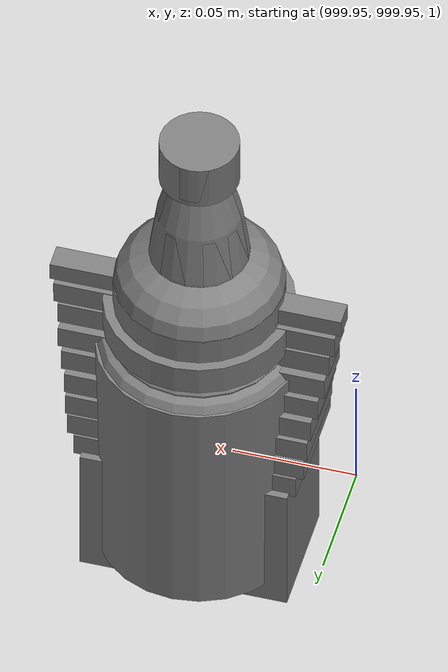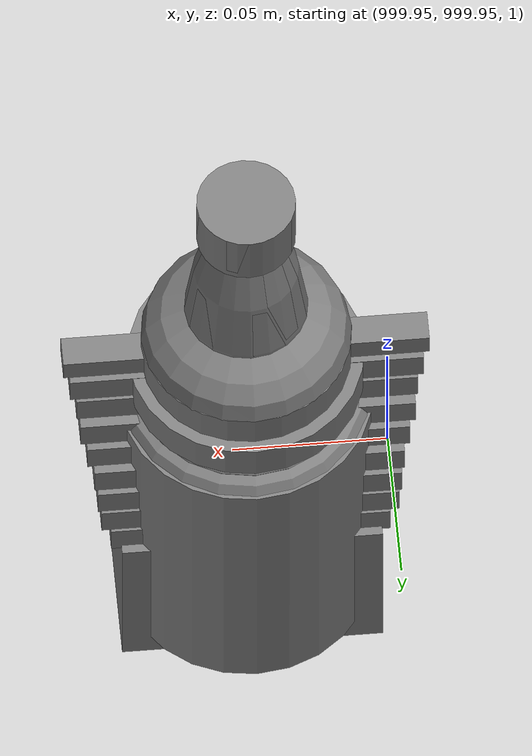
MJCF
<mujoco>
    <option gravity="0.000000000 0.000000000 -9.810000420" timestep="0.0166666" integrator="implicitfast" density="1.225" viscosity="1.8000001e-05" noslip_iterations="10" iterations="100" sdf_iterations="50">
        <flag multiccd="disable"/>
    </option>
    <size memory="1000M"/>
    <compiler coordinate="local"/>
    <worldbody>
        <light cutoff="30" pos="0 1 1" dir="0 -1 -2"/>
        <light cutoff="30" pos="0 -1 1" dir="0 1 -2"/>
        <body pos="-7.168000221 2.823999882 1.227496982" euler="-0.283413976 0.056829724 -0.133293271" name="openloong_gripper_2f85_fix_base_usda_Pos">
            <geom contype="1" conaffinity="1" density="1000" type="box" material="" rgba="0.500000000 0.500000000 0.500000000 1.000000000" solimp="0.899999976 0.949999988 0.001000000" friction="1.000000000 0.005000000 0.000100000" solref="0.020000000 1.000000000" margin="0" condim="3" group="0" pos="-0.002278805 0.074524641 -0.004134059" quat="0.315989345 0.948763072 -0.000000000 0.000000000" size="0.059999999 0.013000000 0.035000000" name="openloong_gripper_2f85_fix_base_usda_geom_BAE0B017_4109_4AC4_8103_838F1AE6ABAB"/>
            <geom contype="1" conaffinity="1" density="1000" type="box" material="" rgba="0.500000000 0.500000000 0.500000000 1.000000000" solimp="0.899999976 0.949999988 0.001000000" friction="1.000000000 0.005000000 0.000100000" solref="0.020000000 1.000000000" margin="0" condim="3" group="0" pos="-0.002278805 0.078031301 0.008128285" quat="0.990447521 -0.137893379 -0.000000000 -0.000000000" size="0.059999999 0.010000000 0.035000000" name="openloong_gripper_2f85_fix_base_usda_geom_B3F71110_2DE2_452B_88F5_E68B190C6799"/>
            <geom contype="1" conaffinity="1" density="1000" type="box" material="" rgba="0.500000000 0.500000000 0.500000000 1.000000000" solimp="0.899999976 0.949999988 0.001000000" friction="1.000000000 0.005000000 0.000100000" solref="0.020000000 1.000000000" margin="0" condim="3" group="0" pos="-0.002278805 0.080785275 -0.002596974" quat="0.287325472 -0.957833409 0.000000000 -0.000000000" size="0.059999999 0.013000000 0.035000000" name="openloong_gripper_2f85_fix_base_usda_geom_0E5C6051_C3A5_4D19_93F0_4A2B1C362EA0"/>
            <geom contype="1" conaffinity="1" density="1000" type="box" material="" rgba="0.500000000 0.500000000 0.500000000 1.000000000" solimp="0.899999976 0.949999988 0.001000000" friction="1.000000000 0.005000000 0.000100000" solref="0.020000000 1.000000000" margin="0" condim="3" group="0" pos="-0.002278805 -0.098804474 -0.020146966" quat="0.988851666 0.148906454 0.000000000 -0.000000000" size="0.059999999 0.022000000 0.020000000" name="openloong_gripper_2f85_fix_base_usda_geom_B3F07113_E0B9_41CC_BA64_F159B2B1935F"/>
            <geom contype="1" conaffinity="1" density="1000" type="box" material="" rgba="0.500000000 0.500000000 0.500000000 1.000000000" solimp="0.899999976 0.949999988 0.001000000" friction="1.000000000 0.005000000 0.000100000" solref="0.020000000 1.000000000" margin="0" condim="3" group="0" pos="-0.002279282 0.019920111 0.012102962" quat="0.995421767 0.095583342 -0.000000000 -0.000000000" size="0.059999999 0.025000000 0.026000001" name="openloong_gripper_2f85_fix_base_usda_geom_3CBCE8CB_69F5_4E5B_AAEA_A81501F5A4CE"/>
            <geom contype="1" conaffinity="1" density="1000" type="box" material="" rgba="0.500000000 0.500000000 0.500000000 1.000000000" solimp="0.899999976 0.949999988 0.001000000" friction="1.000000000 0.005000000 0.000100000" solref="0.020000000 1.000000000" margin="0" condim="3" group="0" pos="-0.002279282 0.005734444 -0.014276862" quat="0.999571741 -0.029275302 -0.000000000 -0.000000000" size="0.059999999 0.050000001 0.010000000" name="openloong_gripper_2f85_fix_base_usda_geom_70993078_621D_493C_A0EF_78DB7702CFD2"/>
            <geom contype="1" conaffinity="1" density="1000" type="box" material="" rgba="0.500000000 0.500000000 0.500000000 1.000000000" solimp="0.899999976 0.949999988 0.001000000" friction="1.000000000 0.005000000 0.000100000" solref="0.020000000 1.000000000" margin="0" condim="3" group="0" pos="-0.002278805 0.079460382 0.007771969" quat="0.922590554 -0.385781586 0.000000000 -0.000000000" size="0.059999999 0.010000000 0.035000000" name="openloong_gripper_2f85_fix_base_usda_geom_C4E209AB_989E_4F0A_9912_7D53FCF34EA6"/>
            <geom contype="1" conaffinity="1" density="1000" type="box" material="" rgba="0.500000000 0.500000000 0.500000000 1.000000000" solimp="0.899999976 0.949999988 0.001000000" friction="1.000000000 0.005000000 0.000100000" solref="0.020000000 1.000000000" margin="0" condim="3" group="0" pos="-0.002279282 0.081384182 -0.001320124" quat="0.590483785 -0.807049930 0.000000000 -0.000000000" size="0.059999999 0.013000000 0.035000000" name="openloong_gripper_2f85_fix_base_usda_geom_5B4A2D41_A78B_4A9C_870F_93910884C0BE"/>
            <geom contype="1" conaffinity="1" density="1000" type="box" material="" rgba="0.500000000 0.500000000 0.500000000 1.000000000" solimp="0.899999976 0.949999988 0.001000000" friction="1.000000000 0.005000000 0.000100000" solref="0.020000000 1.000000000" margin="0" condim="3" group="0" pos="-0.002278805 -0.059297800 -0.007972836" quat="0.988851666 0.148906454 0.000000000 -0.000000000" size="0.059999999 0.020000000 0.022000000" name="openloong_gripper_2f85_fix_base_usda_geom_1E83FA76_DF74_4ED6_A2FE_2402D39CCA8B"/>
            <geom contype="1" conaffinity="1" density="1000" type="box" material="" rgba="0.500000000 0.500000000 0.500000000 1.000000000" solimp="0.899999976 0.949999988 0.001000000" friction="1.000000000 0.005000000 0.000100000" solref="0.020000000 1.000000000" margin="0" condim="3" group="0" pos="-0.002278805 0.076618671 -0.004656792" quat="0.004634961 0.999989629 -0.000000000 0.000000000" size="0.059999999 0.013000000 0.035000000" name="openloong_gripper_2f85_fix_base_usda_geom_6FB97045_F513_4BEC_9646_6960676B91BE"/>
            <geom contype="1" conaffinity="1" density="1000" type="box" material="" rgba="0.500000000 0.500000000 0.500000000 1.000000000" solimp="0.899999976 0.949999988 0.001000000" friction="1.000000000 0.005000000 0.000100000" solref="0.020000000 1.000000000" margin="0" condim="3" group="0" pos="-0.002279282 -0.021952629 0.002960086" quat="0.991270423 0.131847665 -0.000000000 0.000000000" size="0.059999999 0.020000000 0.024000000" name="openloong_gripper_2f85_fix_base_usda_geom_0EFC8271_5BB3_4784_884B_826CF638E642"/>
            <geom contype="1" conaffinity="1" density="1000" type="box" material="" rgba="0.500000000 0.500000000 0.500000000 1.000000000" solimp="0.899999976 0.949999988 0.001000000" friction="1.000000000 0.005000000 0.000100000" solref="0.020000000 1.000000000" margin="0" condim="3" group="0" pos="-0.002278805 0.081418991 0.002587914" quat="0.803492308 -0.595315695 0.000000000 -0.000000000" size="0.059999999 0.013000000 0.035000000" name="openloong_gripper_2f85_fix_base_usda_geom_93FBB272_1963_40F0_9A75_85632DAB7F44"/>
            <geom contype="1" conaffinity="1" density="1000" type="box" material="" rgba="0.500000000 0.500000000 0.500000000 1.000000000" solimp="0.899999976 0.949999988 0.001000000" friction="1.000000000 0.005000000 0.000100000" solref="0.020000000 1.000000000" margin="0" condim="3" group="0" pos="-0.002278805 0.061115503 0.008545756" quat="0.999326169 0.036714450 0.000000000 -0.000000000" size="0.059999999 0.020000000 0.035000000" name="openloong_gripper_2f85_fix_base_usda_geom_5518E04E_5C9B_43DB_942D_479F6B33C8F8"/>
            <freejoint name="openloong_gripper_2f85_fix_base_usda_pos_scan"/>
        </body>
        <body pos="-1.821376681 6.001718044 1.707493305" euler="-30.433002472 -6.522766113 107.648445129" mocap="true" name="spotlight3_SpotLight"/>
        <body pos="1000.000000000 1000.000000000 1.000000000" euler="0.000000000 0.000000000 0.000000000" name="openloong_gripper_2f85_fix_base_usda_bottle_blue">
            <geom contype="1" conaffinity="1" density="1000" type="ellipsoid" material="" rgba="0.500000000 0.500000000 0.500000000 1.000000000" solimp="0.899999976 0.949999988 0.001000000" friction="1.000000000 0.005000000 0.000100000" solref="0.020000000 1.000000000" margin="0" condim="3" group="0" pos="0.000000000 0.000000000 0.118920922" quat="1.000000000 0.000000000 0.000000000 0.000000000" size="0.030999999 0.030999999 0.029999999" name="openloong_gripper_2f85_fix_base_usda_geom_AB86FDC2_7A5C_48B9_97AE_12890C06A06D"/>
            <geom contype="1" conaffinity="1" density="1000" type="box" material="" rgba="0.500000000 0.500000000 0.500000000 1.000000000" solimp="0.899999976 0.949999988 0.001000000" friction="1.000000000 0.005000000 0.000100000" solref="0.020000000 1.000000000" margin="0" condim="3" group="0" pos="0.000000000 0.000000000 0.002164602" quat="1.000000000 0.000000000 0.000000000 0.000000000" size="0.020000000 0.020000000 0.003000000" name="openloong_gripper_2f85_fix_base_usda_geom_B477E40B_F2EF_491A_867D_64379FFAC99A"/>
            <geom contype="1" conaffinity="1" density="1000" type="cylinder" material="" rgba="0.500000000 0.500000000 0.500000000 1.000000000" solimp="0.899999976 0.949999988 0.001000000" friction="1.000000000 0.005000000 0.000100000" solref="0.020000000 1.000000000" margin="0" condim="3" group="0" pos="0.000000000 -0.000366211 0.060859680" quat="1.000000000 0.000000000 0.000000000 0.000000000" size="0.030999999 0.057999998 1.000000000" name="openloong_gripper_2f85_fix_base_usda_geom_349E897F_2EAD_4214_BF75_0E4FEE35E1A7"/>
            <geom contype="1" conaffinity="1" density="1000" type="cylinder" material="" rgba="0.500000000 0.500000000 0.500000000 1.000000000" solimp="0.899999976 0.949999988 0.001000000" friction="1.000000000 0.005000000 0.000100000" solref="0.020000000 1.000000000" margin="0" condim="3" group="0" pos="0.000000000 0.000000000 0.220594406" quat="1.000000000 0.000000000 0.000000000 0.000000000" size="0.016000001 0.010000000 1.000000000" name="openloong_gripper_2f85_fix_base_usda_geom_843B8F57_40AD_4B16_87DB_35357AF28D91"/>
            <geom contype="1" conaffinity="1" density="1000" type="ellipsoid" material="" rgba="0.500000000 0.500000000 0.500000000 1.000000000" solimp="0.899999976 0.949999988 0.001000000" friction="1.000000000 0.005000000 0.000100000" solref="0.020000000 1.000000000" margin="0" condim="3" group="0" pos="0.000000000 0.000000000 0.144259930" quat="1.000000000 0.000000000 0.000000000 0.000000000" size="0.021000000 0.021000000 0.079999998" name="openloong_gripper_2f85_fix_base_usda_geom_71007369_0FD6_44E7_9990_85C20A6AF7DC"/>
            <freejoint name="openloong_gripper_2f85_fix_base_usda_bottle_blue_joint"/>
            <site size="0.005000000 0.005000000 0.005000000" rgba="0.500000000 0.500000000 0.500000000 1.000000000" pos="0.000000000 0.000000000 0.000000000" quat="0.999961913 0.008726535 0.000000000 0.000000000" group="0" type="sphere" name="openloong_gripper_2f85_fix_base_usda_bottle_bluesite"/>
        </body>
        <body pos="1000.000000000 1000.000000000 1.000000000" euler="0.000000000 0.000000000 0.000000000" name="openloong_gripper_2f85_fix_base_usda_jar_01">
            <geom contype="1" conaffinity="1" density="1000" type="box" material="" rgba="0.500000000 0.500000000 0.500000000 1.000000000" solimp="0.899999976 0.949999988 0.001000000" friction="1.000000000 0.005000000 0.000100000" solref="0.020000000 1.000000000" margin="0" condim="3" group="0" pos="0.000000000 0.000000000 0.006158113" quat="1.000000000 0.000000000 0.000000000 0.000000000" size="0.020000000 0.020000000 0.005000000" name="openloong_gripper_2f85_fix_base_usda_geom_78369FC1_2208_4F92_8BD4_70138428E39F"/>
            <geom contype="1" conaffinity="1" density="1000" type="cylinder" material="" rgba="0.500000000 0.500000000 0.500000000 1.000000000" solimp="0.899999976 0.949999988 0.001000000" friction="1.000000000 0.005000000 0.000100000" solref="0.020000000 1.000000000" margin="0" condim="3" group="0" pos="0.000000000 0.000000000 0.062744498" quat="1.000000000 0.000000000 0.000000000 0.000000000" size="0.041000001 0.052999999 1.000000000" name="openloong_gripper_2f85_fix_base_usda_geom_05C28D1A_E753_4AA9_B0A0_F9631034F96B"/>
            <geom contype="1" conaffinity="1" density="1000" type="ellipsoid" material="" rgba="0.500000000 0.500000000 0.500000000 1.000000000" solimp="0.899999976 0.949999988 0.001000000" friction="1.000000000 0.005000000 0.000100000" solref="0.020000000 1.000000000" margin="0" condim="3" group="0" pos="0.000000000 0.000000000 0.122252703" quat="1.000000000 0.000000000 0.000000000 0.000000000" size="0.035999998 0.035999998 0.010000000" name="openloong_gripper_2f85_fix_base_usda_geom_5BA10C85_3D54_4C5B_91E2_9CFFE6365560"/>
            <geom contype="1" conaffinity="1" density="1000" type="cylinder" material="" rgba="0.500000000 0.500000000 0.500000000 1.000000000" solimp="0.899999976 0.949999988 0.001000000" friction="1.000000000 0.005000000 0.000100000" solref="0.020000000 1.000000000" margin="0" condim="3" group="0" pos="0.000000000 0.000000000 0.015747190" quat="1.000000000 0.000000000 0.000000000 0.000000000" size="0.035000000 0.010000000 1.000000000" name="openloong_gripper_2f85_fix_base_usda_geom_1659A1E7_CE68_4404_B21E_A97B8F2AE3AB"/>
            <geom contype="1" conaffinity="1" density="1000" type="ellipsoid" material="" rgba="0.500000000 0.500000000 0.500000000 1.000000000" solimp="0.899999976 0.949999988 0.001000000" friction="1.000000000 0.005000000 0.000100000" solref="0.020000000 1.000000000" margin="0" condim="3" group="0" pos="0.000000000 0.000000000 0.115815401" quat="1.000000000 0.000000000 0.000000000 0.000000000" size="0.039999999 0.039999999 0.010000000" name="openloong_gripper_2f85_fix_base_usda_geom_B9FC1F60_2534_441D_B128_4D1E555AFC38"/>
            <geom contype="1" conaffinity="1" density="1000" type="cylinder" material="" rgba="0.500000000 0.500000000 0.500000000 1.000000000" solimp="0.899999976 0.949999988 0.001000000" friction="1.000000000 0.005000000 0.000100000" solref="0.020000000 1.000000000" margin="0" condim="3" group="0" pos="0.000000000 0.000000000 0.133183479" quat="1.000000000 0.000000000 0.000000000 0.000000000" size="0.037999999 0.006500000 1.000000000" name="openloong_gripper_2f85_fix_base_usda_geom_1C51D419_8781_49F5_82A6_075E005C4E8A"/>
            <freejoint name="openloong_gripper_2f85_fix_base_usda_jar_01_joint"/>
            <site size="0.005000000 0.005000000 0.005000000" rgba="0.500000000 0.500000000 0.500000000 1.000000000" pos="0.000000000 0.000000000 0.000000000" quat="1.000000000 0.000000000 0.000000000 0.000000000" group="0" type="sphere" name="openloong_gripper_2f85_fix_base_usda_jar_01site"/>
        </body>
        <body pos="1000.000000000 1000.000000000 1.000000000" euler="0.000000000 0.000000000 0.000000000" name="openloong_gripper_2f85_fix_base_usda_salt">
            <geom contype="1" conaffinity="1" density="1000" type="box" material="" rgba="0.500000000 0.500000000 0.500000000 1.000000000" solimp="0.899999976 0.949999988 0.001000000" friction="1.000000000 0.005000000 0.000100000" solref="0.020000000 1.000000000" margin="0" condim="3" group="0" pos="0.000305176 0.000000000 0.084862232" quat="1.000000000 0.000000000 0.000000000 0.000000000" size="0.048999999 0.018999999 0.005000000" name="openloong_gripper_2f85_fix_base_usda_geom_9C71AB48_FD66_44D2_A1E1_E004393F6E66"/>
            <geom contype="1" conaffinity="1" density="1000" type="box" material="" rgba="0.500000000 0.500000000 0.500000000 1.000000000" solimp="0.899999976 0.949999988 0.001000000" friction="1.000000000 0.005000000 0.000100000" solref="0.020000000 1.000000000" margin="0" condim="3" group="0" pos="0.000305176 0.000000000 0.104564309" quat="1.000000000 0.000000000 0.000000000 0.000000000" size="0.052000001 0.014000000 0.005000000" name="openloong_gripper_2f85_fix_base_usda_geom_9F58D4AB_3823_492B_BD8D_4848F49C059A"/>
            <geom contype="1" conaffinity="1" density="1000" type="box" material="" rgba="0.500000000 0.500000000 0.500000000 1.000000000" solimp="0.899999976 0.949999988 0.001000000" friction="1.000000000 0.005000000 0.000100000" solref="0.020000000 1.000000000" margin="0" condim="3" group="0" pos="0.000305176 0.000000000 0.114487171" quat="1.000000000 0.000000000 0.000000000 0.000000000" size="0.054000001 0.011500000 0.005000000" name="openloong_gripper_2f85_fix_base_usda_geom_4A2BAF4B_A820_4E7B_8E5A_3F7510AD6A14"/>
            <geom contype="1" conaffinity="1" density="1000" type="box" material="" rgba="0.500000000 0.500000000 0.500000000 1.000000000" solimp="0.899999976 0.949999988 0.001000000" friction="1.000000000 0.005000000 0.000100000" solref="0.020000000 1.000000000" margin="0" condim="3" group="0" pos="0.000305176 0.000000000 0.075103164" quat="1.000000000 0.000000000 0.000000000 0.000000000" size="0.048000000 0.020000000 0.005000000" name="openloong_gripper_2f85_fix_base_usda_geom_1B9D1D3C_91E3_4DC9_9E48_E9DAE61697CC"/>
            <geom contype="1" conaffinity="1" density="1000" type="box" material="" rgba="0.500000000 0.500000000 0.500000000 1.000000000" solimp="0.899999976 0.949999988 0.001000000" friction="1.000000000 0.005000000 0.000100000" solref="0.020000000 1.000000000" margin="0" condim="3" group="0" pos="0.000305176 0.000000000 0.134892464" quat="1.000000000 0.000000000 0.000000000 0.000000000" size="0.057000000 0.007000000 0.005000000" name="openloong_gripper_2f85_fix_base_usda_geom_4D85FC78_E407_4433_9249_D329A1E86CD1"/>
            <geom contype="1" conaffinity="1" density="1000" type="box" material="" rgba="0.500000000 0.500000000 0.500000000 1.000000000" solimp="0.899999976 0.949999988 0.001000000" friction="1.000000000 0.005000000 0.000100000" solref="0.020000000 1.000000000" margin="0" condim="3" group="0" pos="0.000305176 0.000000000 0.094920278" quat="1.000000000 0.000000000 0.000000000 0.000000000" size="0.050000001 0.017000001 0.005000000" name="openloong_gripper_2f85_fix_base_usda_geom_BF37ABF0_A903_486E_AF7A_2D432CBCD7FA"/>
            <geom contype="1" conaffinity="1" density="1000" type="box" material="" rgba="0.500000000 0.500000000 0.500000000 1.000000000" solimp="0.899999976 0.949999988 0.001000000" friction="1.000000000 0.005000000 0.000100000" solref="0.020000000 1.000000000" margin="0" condim="3" group="0" pos="0.000305176 0.000000000 0.065204859" quat="1.000000000 0.000000000 0.000000000 0.000000000" size="0.045000002 0.021000000 0.005000000" name="openloong_gripper_2f85_fix_base_usda_geom_8A73448B_E4FF_4638_A7AE_A7183D9B4E36"/>
            <geom contype="1" conaffinity="1" density="1000" type="box" material="" rgba="0.500000000 0.500000000 0.500000000 1.000000000" solimp="0.899999976 0.949999988 0.001000000" friction="1.000000000 0.005000000 0.000100000" solref="0.020000000 1.000000000" margin="0" condim="3" group="0" pos="0.000305176 0.000000000 0.144135714" quat="1.000000000 0.000000000 0.000000000 0.000000000" size="0.059000000 0.005000000 0.004000000" name="openloong_gripper_2f85_fix_base_usda_geom_996246DD_427F_475B_B1DC_8736BAB7AE3F"/>
            <geom contype="1" conaffinity="1" density="1000" type="box" material="" rgba="0.500000000 0.500000000 0.500000000 1.000000000" solimp="0.899999976 0.949999988 0.001000000" friction="1.000000000 0.005000000 0.000100000" solref="0.020000000 1.000000000" margin="0" condim="3" group="0" pos="0.000000000 0.000000000 0.031593561" quat="1.000000000 0.000000000 0.000000000 0.000000000" size="0.041999999 0.024000000 0.029999999" name="openloong_gripper_2f85_fix_base_usda_geom_86571A0E_636E_46EE_AE57_9C607DADC492"/>
            <geom contype="1" conaffinity="1" density="1000" type="box" material="" rgba="0.500000000 0.500000000 0.500000000 1.000000000" solimp="0.899999976 0.949999988 0.001000000" friction="1.000000000 0.005000000 0.000100000" solref="0.020000000 1.000000000" margin="0" condim="3" group="0" pos="0.000305176 0.000000000 0.124608755" quat="1.000000000 0.000000000 0.000000000 0.000000000" size="0.055000000 0.008000000 0.005000000" name="openloong_gripper_2f85_fix_base_usda_geom_F0C89048_7F3A_4346_8322_F5DDD2F30587"/>
            <freejoint name="openloong_gripper_2f85_fix_base_usda_salt_joint"/>
            <site size="0.005000000 0.005000000 0.005000000" rgba="0.500000000 0.500000000 0.500000000 1.000000000" pos="0.000000000 0.000000000 0.000000000" quat="1.000000000 0.000000000 0.000000000 0.000000000" group="0" type="sphere" name="openloong_gripper_2f85_fix_base_usda_saltsite"/>
        </body>
        <body pos="1000.000000000 1000.000000000 1.000000000" euler="0.000000000 0.000000000 0.000000000" name="openloong_gripper_2f85_fix_base_usda_can">
            <geom contype="1" conaffinity="1" density="1000" type="cylinder" material="" rgba="0.500000000 0.500000000 0.500000000 1.000000000" solimp="0.899999976 0.949999988 0.001000000" friction="1.000000000 0.005000000 0.000100000" solref="0.020000000 1.000000000" margin="0" condim="3" group="0" pos="0.000000000 0.000000000 0.079676986" quat="1.000000000 0.000000000 0.000000000 0.000000000" size="0.034000002 0.071999997 1.000000000" name="openloong_gripper_2f85_fix_base_usda_geom_A99F34CC_C47F_42F4_8B4B_0B9C861F5D02"/>
            <geom contype="1" conaffinity="1" density="1000" type="ellipsoid" material="" rgba="0.500000000 0.500000000 0.500000000 1.000000000" solimp="0.899999976 0.949999988 0.001000000" friction="1.000000000 0.005000000 0.000100000" solref="0.020000000 1.000000000" margin="0" condim="3" group="0" pos="0.000000000 0.000000000 0.151854277" quat="1.000000000 0.000000000 0.000000000 0.000000000" size="0.034000002 0.034000002 0.020000000" name="openloong_gripper_2f85_fix_base_usda_geom_7B2D1654_0735_44A2_ABED_779B07888D69"/>
            <geom contype="1" conaffinity="1" density="1000" type="box" material="" rgba="0.500000000 0.500000000 0.500000000 1.000000000" solimp="0.899999976 0.949999988 0.001000000" friction="1.000000000 0.005000000 0.000100000" solref="0.020000000 1.000000000" margin="0" condim="3" group="0" pos="0.000000000 0.000000000 0.004777670" quat="1.000000000 0.000000000 0.000000000 0.000000000" size="0.020000000 0.020000000 0.005000000" name="openloong_gripper_2f85_fix_base_usda_geom_197B013E_004C_40DA_9DA0_17541EE728EB"/>
            <freejoint name="openloong_gripper_2f85_fix_base_usda_can_joint"/>
            <site size="0.005000000 0.005000000 0.005000000" rgba="0.500000000 0.500000000 0.500000000 1.000000000" pos="0.000000000 0.000000000 0.000000000" quat="1.000000000 0.000000000 0.000000000 0.000000000" group="0" type="sphere" name="openloong_gripper_2f85_fix_base_usda_cansite"/>
        </body>
        <body pos="-2.217788696 6.380573750 1.852365255" euler="169.543762207 35.083507538 -97.201980591" mocap="true" name="spotlight1_SpotLight"/>
        <body pos="1000.000000000 1000.000000000 1.000000000" euler="0.000000000 0.000000000 0.000000000" name="openloong_gripper_2f85_fix_base_usda_bottle_red">
            <geom contype="1" conaffinity="1" density="1000" type="ellipsoid" material="" rgba="0.500000000 0.500000000 0.500000000 1.000000000" solimp="0.899999976 0.949999988 0.001000000" friction="1.000000000 0.005000000 0.000100000" solref="0.020000000 1.000000000" margin="0" condim="3" group="0" pos="0.000000000 0.000000000 0.144284487" quat="1.000000000 0.000000000 0.000000000 0.000000000" size="0.021000000 0.021000000 0.079999998" name="openloong_gripper_2f85_fix_base_usda_geom_15D87DF6_A997_46D4_8C31_9D5C1E16D5F3"/>
            <geom contype="1" conaffinity="1" density="1000" type="cylinder" material="" rgba="0.500000000 0.500000000 0.500000000 1.000000000" solimp="0.899999976 0.949999988 0.001000000" friction="1.000000000 0.005000000 0.000100000" solref="0.020000000 1.000000000" margin="0" condim="3" group="0" pos="0.000000000 0.000000000 0.220618963" quat="1.000000000 0.000000000 0.000000000 0.000000000" size="0.016000001 0.010000000 1.000000000" name="openloong_gripper_2f85_fix_base_usda_geom_EB0A7BF0_957E_4285_B91C_2690DBB2B968"/>
            <geom contype="1" conaffinity="1" density="1000" type="ellipsoid" material="" rgba="0.500000000 0.500000000 0.500000000 1.000000000" solimp="0.899999976 0.949999988 0.001000000" friction="1.000000000 0.005000000 0.000100000" solref="0.020000000 1.000000000" margin="0" condim="3" group="0" pos="0.000000000 0.000000000 0.118945479" quat="1.000000000 0.000000000 0.000000000 0.000000000" size="0.030999999 0.030999999 0.029999999" name="openloong_gripper_2f85_fix_base_usda_geom_8799A6C7_1C75_4719_839B_2969ED769064"/>
            <geom contype="1" conaffinity="1" density="1000" type="box" material="" rgba="0.500000000 0.500000000 0.500000000 1.000000000" solimp="0.899999976 0.949999988 0.001000000" friction="1.000000000 0.005000000 0.000100000" solref="0.020000000 1.000000000" margin="0" condim="3" group="0" pos="0.000000000 0.000000000 0.002189159" quat="1.000000000 0.000000000 0.000000000 0.000000000" size="0.020000000 0.020000000 0.003000000" name="openloong_gripper_2f85_fix_base_usda_geom_60D78734_18A6_4C7B_A4CF_788DD89D8BD4"/>
            <geom contype="1" conaffinity="1" density="1000" type="cylinder" material="" rgba="0.500000000 0.500000000 0.500000000 1.000000000" solimp="0.899999976 0.949999988 0.001000000" friction="1.000000000 0.005000000 0.000100000" solref="0.020000000 1.000000000" margin="0" condim="3" group="0" pos="0.000000000 -0.000366211 0.060884237" quat="1.000000000 0.000000000 0.000000000 0.000000000" size="0.030999999 0.057999998 1.000000000" name="openloong_gripper_2f85_fix_base_usda_geom_E4CFAB11_5DD1_4EDB_95A9_BDCF5CCB6D8C"/>
            <freejoint name="openloong_gripper_2f85_fix_base_usda_bottle_red_joint"/>
            <site size="0.005000000 0.005000000 0.005000000" rgba="0.500000000 0.500000000 0.500000000 1.000000000" pos="0.000000000 0.000000000 0.000000000" quat="0.999961913 0.008726535 0.000000000 0.000000000" group="0" type="sphere" name="openloong_gripper_2f85_fix_base_usda_bottle_redsite"/>
        </body>
        <body pos="-2.006907225 6.563029289 1.792693973" euler="57.066406250 52.289421082 -89.917266846" mocap="true" name="spotlight2_SpotLight"/>
        <body pos="0.000000000 0.000000000 0.000000000" euler="0.000000000 0.000000000 0.000000000" name="Interactive Objects_Interactive Objects"/>
        <body pos="0.000000000 0.000000000 0.000000000" euler="0.000000000 0.000000000 0.000000000" name=" Static Objects_ Static Objects">
            <geom contype="1" conaffinity="1" density="1000" type="box" material="" rgba="0.500000000 0.500000000 0.500000000 1.000000000" solimp="0.899999976 0.949999988 0.001000000" friction="1.000000000 0.005000000 0.000100000" solref="0.020000000 1.000000000" margin="0" condim="3" group="0" pos="-6.286010742 6.153595448 1.563861728" quat="0.707107067 0.000000000 0.000000000 0.707106471" size="0.529999971 3.134999990 0.025000000" name=" Static Objects_geom_E4252AB2_D7DC_4D78_937D_D78D59C81421"/>
            <geom contype="1" conaffinity="1" density="1000" type="box" material="" rgba="0.500000000 0.500000000 0.500000000 1.000000000" solimp="0.899999976 0.949999988 0.001000000" friction="1.000000000 0.005000000 0.000100000" solref="0.020000000 1.000000000" margin="0" condim="3" group="0" pos="-3.101639986 6.150595188 1.018643856" quat="1.000000000 0.000000000 0.000000000 0.000000000" size="0.050000001 0.579999983 1.019999981" name=" Static Objects_geom_47AEB040_6B81_401E_924C_3A0A2213DE08"/>
            <geom contype="1" conaffinity="1" density="1000" type="box" material="" rgba="0.500000000 0.500000000 0.500000000 1.000000000" solimp="0.899999976 0.949999988 0.001000000" friction="1.000000000 0.005000000 0.000100000" solref="0.020000000 1.000000000" margin="0" condim="3" group="0" pos="-2.825197220 6.153595448 1.563861728" quat="0.707107067 0.000000000 0.000000000 0.707106471" size="0.550000012 0.239999995 0.025000000" name=" Static Objects_geom_3768425E_E6CC_4007_963B_FD84514F251B"/>
            <geom contype="1" conaffinity="1" density="1000" type="box" material="" rgba="0.500000000 0.500000000 0.500000000 1.000000000" solimp="0.899999976 0.949999988 0.001000000" friction="1.000000000 0.005000000 0.000100000" solref="0.020000000 1.000000000" margin="0" condim="3" group="0" pos="-6.311686516 6.153595448 1.018643856" quat="0.707107067 0.000000000 0.000000000 0.707106471" size="0.050000001 3.150000095 1.019999981" name=" Static Objects_geom_87102682_C517_4355_8129_8465BED2D084"/>
            <geom contype="1" conaffinity="1" density="1000" type="box" material="" rgba="0.500000000 0.500000000 0.500000000 1.000000000" solimp="0.899999976 0.949999988 0.001000000" friction="1.000000000 0.005000000 0.000100000" solref="0.020000000 1.000000000" margin="0" condim="3" group="0" pos="-2.825197220 6.153595448 1.115278244" quat="0.707107067 0.000000000 0.000000000 0.707106471" size="0.550000012 0.239999995 0.025000000" name=" Static Objects_geom_CEE1182C_C7A2_4640_9237_7A8C6BEC570E"/>
            <geom contype="1" conaffinity="1" density="1000" type="box" material="" rgba="0.500000000 0.500000000 0.500000000 1.000000000" solimp="0.899999976 0.949999988 0.001000000" friction="1.000000000 0.005000000 0.000100000" solref="0.020000000 1.000000000" margin="0" condim="3" group="0" pos="-6.293097973 6.153595448 1.114443064" quat="0.707107067 0.000000000 0.000000000 0.707106471" size="0.529999971 3.134999990 0.025000000" name=" Static Objects_geom_8ED5C41E_9C0F_4105_AFBE_D61A0D9059ED"/>
            <geom contype="1" conaffinity="1" density="1000" type="box" material="" rgba="0.500000000 0.500000000 0.500000000 1.000000000" solimp="0.899999976 0.949999988 0.001000000" friction="1.000000000 0.005000000 0.000100000" solref="0.020000000 1.000000000" margin="0" condim="3" group="0" pos="-2.825197220 6.153595448 0.629031777" quat="0.707107067 0.000000000 0.000000000 0.707106471" size="0.550000012 0.239999995 0.025000000" name=" Static Objects_geom_E58F2D5B_34F2_47F1_B8A9_D1B3C6B35A0E"/>
            <geom contype="1" conaffinity="1" density="1000" type="box" material="" rgba="0.500000000 0.500000000 0.500000000 1.000000000" solimp="0.899999976 0.949999988 0.001000000" friction="1.000000000 0.005000000 0.000100000" solref="0.020000000 1.000000000" margin="0" condim="3" group="0" pos="-6.286010742 6.153595448 0.096129179" quat="0.707107067 0.000000000 0.000000000 0.707106471" size="0.529999971 3.134999990 0.098999999" name=" Static Objects_geom_3EEDC9C3_FD50_4AD6_8841_08CBC595AFA3"/>
            <geom contype="1" conaffinity="1" density="1000" type="box" material="" rgba="0.500000000 0.500000000 0.500000000 1.000000000" solimp="0.899999976 0.949999988 0.001000000" friction="1.000000000 0.005000000 0.000100000" solref="0.020000000 1.000000000" margin="0" condim="3" group="0" pos="-2.825197220 6.153595448 0.097434282" quat="0.707107067 0.000000000 0.000000000 0.707106471" size="0.550000012 0.239999995 0.098999999" name=" Static Objects_geom_1E2D8DA2_6CF0_444E_9AB1_08BF3AF00D7E"/>
            <geom contype="1" conaffinity="1" density="1000" type="box" material="" rgba="0.500000000 0.500000000 0.500000000 1.000000000" solimp="0.899999976 0.949999988 0.001000000" friction="1.000000000 0.005000000 0.000100000" solref="0.020000000 1.000000000" margin="0" condim="3" group="0" pos="-6.286010742 6.153595448 0.629031777" quat="0.707107067 0.000000000 0.000000000 0.707106471" size="0.529999971 3.134999990 0.025000000" name=" Static Objects_geom_1438B6A5_A6DD_411A_8F4C_C3A74418893E"/>
            <geom contype="1" conaffinity="1" density="1000" type="box" material="" rgba="0.500000000 0.500000000 0.500000000 1.000000000" solimp="0.899999976 0.949999988 0.001000000" friction="1.000000000 0.005000000 0.000100000" solref="0.020000000 1.000000000" margin="0" condim="3" group="0" pos="-6.000000000 20.159999847 2.000000000" quat="1.000000000 0.000000000 0.000000000 0.000000000" size="6.079999924 0.070000000 2.000000000" name=" Static Objects_geom_DE427335_8B11_4D0C_AE2F_CD0058A96A1B"/>
            <geom contype="1" conaffinity="1" density="1000" type="box" material="" rgba="0.500000000 0.500000000 0.500000000 1.000000000" solimp="0.899999976 0.949999988 0.001000000" friction="1.000000000 0.005000000 0.000100000" solref="0.020000000 1.000000000" margin="0" condim="3" group="0" pos="-6.000000000 0.035000000 2.000000000" quat="1.000000000 0.000000000 0.000000000 0.000000000" size="6.079999924 0.070000000 2.000000000" name=" Static Objects_geom_6A7F4406_9DB0_4EB6_A603_FE6067821AA7"/>
            <geom contype="1" conaffinity="1" density="1000" type="box" material="" rgba="0.500000000 0.500000000 0.500000000 1.000000000" solimp="0.899999976 0.949999988 0.001000000" friction="1.000000000 0.005000000 0.000100000" solref="0.020000000 1.000000000" margin="0" condim="3" group="0" pos="0.000000000 10.000000000 2.000000000" quat="1.000000000 0.000000000 0.000000000 0.000000000" size="0.070000000 10.500000000 2.000000000" name=" Static Objects_geom_771089F5_6D0B_42B6_8596_9D2DD1BE87B9"/>
            <geom contype="1" conaffinity="1" density="1000" type="box" material="" rgba="0.500000000 0.500000000 0.500000000 1.000000000" solimp="0.899999976 0.949999988 0.001000000" friction="1.000000000 0.005000000 0.000100000" solref="0.020000000 1.000000000" margin="0" condim="3" group="0" pos="-12.050000191 10.000000000 2.000000000" quat="1.000000000 0.000000000 0.000000000 0.000000000" size="0.070000000 10.500000000 2.000000000" name=" Static Objects_geom_D287325F_CF93_4DC4_8506_7DF979CF1D16"/>
            <geom contype="1" conaffinity="1" density="1000" type="plane" material="" rgba="0.500000000 0.500000000 0.500000000 1.000000000" solimp="0.899999976 0.949999988 0.001000000" friction="1.000000000 0.005000000 0.000100000" solref="0.020000000 1.000000000" margin="0" condim="3" group="0" pos="-6.000000000 10.399999619 0.000000000" quat="1.000000000 0.000000000 0.000000000 0.000000000" size="6.050000191 10.800000191 0.010000000" name=" Static Objects_geom_F1B06953_3F05_47D0_8F2B_EB66EBF476E2"/>
            <geom contype="1" conaffinity="1" density="1000" type="box" material="" rgba="0.500000000 0.500000000 0.500000000 1.000000000" solimp="0.899999976 0.949999988 0.001000000" friction="1.000000000 0.005000000 0.000100000" solref="0.020000000 1.000000000" margin="0" condim="3" group="0" pos="-8.830721855 2.096410990 0.549305558" quat="1.000000000 0.000000000 0.000000000 0.000000000" size="0.280000001 0.430000007 0.550000012" name=" Static Objects_geom_20AEF0C1_80D8_4AA7_8823_9CD3C38E4D87"/>
            <geom contype="1" conaffinity="1" density="1000" type="box" material="" rgba="0.500000000 0.500000000 0.500000000 1.000000000" solimp="0.899999976 0.949999988 0.001000000" friction="1.000000000 0.005000000 0.000100000" solref="0.020000000 1.000000000" margin="0" condim="3" group="0" pos="-6.460197449 2.937205315 0.548931718" quat="1.000000000 0.000000000 0.000000000 0.000000000" size="2.650000095 0.430000007 0.550000012" name=" Static Objects_geom_C8DA66E9_5FD9_46C0_BAB2_480FF1EACA43"/>
            <geom contype="1" conaffinity="1" density="1000" type="box" material="" rgba="0.500000000 0.500000000 0.500000000 1.000000000" solimp="0.899999976 0.949999988 0.001000000" friction="1.000000000 0.005000000 0.000100000" solref="0.020000000 1.000000000" margin="0" condim="3" group="0" pos="-4.240264893 1.327049494 0.549888909" quat="1.000000000 0.000000000 0.000000000 0.000000000" size="0.430000007 1.200000048 0.550000012" name=" Static Objects_geom_735C70E2_1C6A_4A8B_86F0_A37750653CD7"/>
            <geom contype="1" conaffinity="1" density="1000" type="box" material="" rgba="0.500000000 0.500000000 0.500000000 1.000000000" solimp="0.899999976 0.949999988 0.001000000" friction="1.000000000 0.005000000 0.000100000" solref="0.020000000 1.000000000" margin="0" condim="3" group="0" pos="-7.408766270 3.088089943 1.776644945" quat="0.928051054 0.000000000 0.000000000 0.372453064" size="0.050000001 0.100000001 0.050000001" name=" Static Objects_geom_D68CDD3F_F875_4961_9102_42FC5DC091FE"/>
            <geom contype="1" conaffinity="1" density="1000" type="box" material="" rgba="0.500000000 0.500000000 0.500000000 1.000000000" solimp="0.899999976 0.949999988 0.001000000" friction="1.000000000 0.005000000 0.000100000" solref="0.020000000 1.000000000" margin="0" condim="3" group="0" pos="-7.437745571 3.067511320 1.289965630" quat="1.000000000 0.000000000 0.000000000 0.000000000" size="0.029999999 0.020000000 0.020000000" name=" Static Objects_geom_F5E8AEE1_77D3_42A6_AD51_D6748648A216"/>
            <geom contype="1" conaffinity="1" density="1000" type="box" material="" rgba="0.500000000 0.500000000 0.500000000 1.000000000" solimp="0.899999976 0.949999988 0.001000000" friction="1.000000000 0.005000000 0.000100000" solref="0.020000000 1.000000000" margin="0" condim="3" group="0" pos="-7.719123363 2.867671013 1.173410416" quat="1.000000000 0.000000000 0.000000000 0.000000000" size="0.250000000 0.250000000 0.079999998" name=" Static Objects_geom_1170F467_FE0E_4DCE_ACF1_E84118D6B5D1"/>
            <geom contype="1" conaffinity="1" density="1000" type="box" material="" rgba="0.500000000 0.500000000 0.500000000 1.000000000" solimp="0.899999976 0.949999988 0.001000000" friction="1.000000000 0.005000000 0.000100000" solref="0.020000000 1.000000000" margin="0" condim="3" group="0" pos="-7.719123363 2.958004713 1.530241251" quat="1.000000000 0.000000000 0.000000000 0.000000000" size="0.250000000 0.159999996 0.280000001" name=" Static Objects_geom_E6B40572_9CF7_47DF_8269_8D53081B611C"/>
            <geom contype="1" conaffinity="1" density="1000" type="cylinder" material="" rgba="0.500000000 0.500000000 0.500000000 1.000000000" solimp="0.899999976 0.949999988 0.001000000" friction="1.000000000 0.005000000 0.000100000" solref="0.020000000 1.000000000" margin="0" condim="3" group="0" pos="-7.427312374 3.069516420 1.502544641" quat="0.928051054 0.000000000 0.000000000 0.372453064" size="0.015000000 0.230000004 0.100000001" name=" Static Objects_geom_3CDC7B29_7D0E_433C_87C4_A3EDF7BCC9C0"/>
            <geom contype="1" conaffinity="1" density="1000" type="box" material="" rgba="0.500000000 0.500000000 0.500000000 1.000000000" solimp="0.899999976 0.949999988 0.001000000" friction="1.000000000 0.005000000 0.000100000" solref="0.020000000 1.000000000" margin="0" condim="3" group="0" pos="-9.058088303 6.434794426 1.209077358" quat="1.000000000 0.000000000 0.000000000 0.000000000" size="0.250000000 0.100000001 0.070000000" name=" Static Objects_geom_3D4ABC21_4C6E_4316_9AAD_50087887A2A7"/>
            <geom contype="1" conaffinity="1" density="1000" type="box" material="" rgba="0.500000000 0.500000000 0.500000000 1.000000000" solimp="0.899999976 0.949999988 0.001000000" friction="1.000000000 0.005000000 0.000100000" solref="0.020000000 1.000000000" margin="0" condim="3" group="0" pos="-5.611940861 6.318420410 0.350975692" quat="1.000000000 0.000000000 0.000000000 0.000000000" size="0.699999988 0.100000001 0.150000006" name=" Static Objects_geom_BFD22E33_7C5B_49D0_80FE_0C243B43C425"/>
            <geom contype="1" conaffinity="1" density="1000" type="box" material="" rgba="0.500000000 0.500000000 0.500000000 1.000000000" solimp="0.899999976 0.949999988 0.001000000" friction="1.000000000 0.005000000 0.000100000" solref="0.020000000 1.000000000" margin="0" condim="3" group="0" pos="-9.237723351 6.464855671 1.209077358" quat="1.000000000 0.000000000 0.000000000 0.000000000" size="0.100000001 0.100000001 0.070000000" name=" Static Objects_geom_DBA7BA2B_3F07_4C7D_B7C5_8E663F62DBC6"/>
            <geom contype="1" conaffinity="1" density="1000" type="box" material="" rgba="0.500000000 0.500000000 0.500000000 1.000000000" solimp="0.899999976 0.949999988 0.001000000" friction="1.000000000 0.005000000 0.000100000" solref="0.020000000 1.000000000" margin="0" condim="3" group="0" pos="-6.300771236 6.459744930 1.744376063" quat="1.000000000 0.000000000 0.000000000 0.000000000" size="3.000000000 0.200000003 0.150000006" name=" Static Objects_geom_677BE011_C7C7_4FC7_97BB_03372804B9D7"/>
            <geom contype="1" conaffinity="1" density="1000" type="box" material="" rgba="0.500000000 0.500000000 0.500000000 1.000000000" solimp="0.899999976 0.949999988 0.001000000" friction="1.000000000 0.005000000 0.000100000" solref="0.020000000 1.000000000" margin="0" condim="3" group="0" pos="-7.373087406 6.458900928 1.214329123" quat="1.000000000 0.000000000 0.000000000 0.000000000" size="0.250000000 0.200000003 0.075000003" name=" Static Objects_geom_8466FACB_7D6F_407A_AC6B_BE54C26999D1"/>
            <geom contype="1" conaffinity="1" density="1000" type="box" material="" rgba="0.500000000 0.500000000 0.500000000 1.000000000" solimp="0.899999976 0.949999988 0.001000000" friction="1.000000000 0.005000000 0.000100000" solref="0.020000000 1.000000000" margin="0" condim="3" group="0" pos="-4.035642624 6.459744930 0.352518857" quat="1.000000000 0.000000000 0.000000000 0.000000000" size="0.800000012 0.200000003 0.150000006" name=" Static Objects_geom_45586CF0_97D0_4B5E_AADF_388E22F149D0"/>
            <geom contype="1" conaffinity="1" density="1000" type="box" material="" rgba="0.500000000 0.500000000 0.500000000 1.000000000" solimp="0.899999976 0.949999988 0.001000000" friction="1.000000000 0.005000000 0.000100000" solref="0.020000000 1.000000000" margin="0" condim="3" group="0" pos="-3.907610416 6.318625927 0.800981164" quat="1.000000000 0.000000000 0.000000000 0.000000000" size="0.500000000 0.100000001 0.150000006" name=" Static Objects_geom_CEEE4570_92C4_4C44_A156_2DAB6AED1C7F"/>
            <geom contype="1" conaffinity="1" density="1000" type="box" material="" rgba="0.500000000 0.500000000 0.500000000 1.000000000" solimp="0.899999976 0.949999988 0.001000000" friction="1.000000000 0.005000000 0.000100000" solref="0.020000000 1.000000000" margin="0" condim="3" group="0" pos="-6.098561764 6.327973843 1.292199373" quat="1.000000000 0.000000000 0.000000000 0.000000000" size="0.500000000 0.100000001 0.150000006" name=" Static Objects_geom_B8E8A189_171A_46F8_A1E4_7931BB59AD3C"/>
            <geom contype="1" conaffinity="1" density="1000" type="box" material="" rgba="0.500000000 0.500000000 0.500000000 1.000000000" solimp="0.899999976 0.949999988 0.001000000" friction="1.000000000 0.005000000 0.000100000" solref="0.020000000 1.000000000" margin="0" condim="3" group="0" pos="-7.886891365 6.459744930 0.352518857" quat="1.000000000 0.000000000 0.000000000 0.000000000" size="1.500000000 0.200000003 0.150000006" name=" Static Objects_geom_BDFEA867_3584_4E96_B050_3D3809B4F236"/>
            <geom contype="1" conaffinity="1" density="1000" type="box" material="" rgba="0.500000000 0.500000000 0.500000000 1.000000000" solimp="0.899999976 0.949999988 0.001000000" friction="1.000000000 0.005000000 0.000100000" solref="0.020000000 1.000000000" margin="0" condim="3" group="0" pos="-6.824534416 6.447464466 1.212718010" quat="1.000000000 0.000000000 0.000000000 0.000000000" size="0.100000001 0.100000001 0.075000003" name=" Static Objects_geom_585842F9_394A_475B_9C1E_5AC2EEC8C40D"/>
            <geom contype="1" conaffinity="1" density="1000" type="box" material="" rgba="0.500000000 0.500000000 0.500000000 1.000000000" solimp="0.899999976 0.949999988 0.001000000" friction="1.000000000 0.005000000 0.000100000" solref="0.020000000 1.000000000" margin="0" condim="3" group="0" pos="-4.407354832 6.459744930 1.292199373" quat="1.000000000 0.000000000 0.000000000 0.000000000" size="1.240000010 0.200000003 0.150000006" name=" Static Objects_geom_356E1651_F45B_4E71_82FD_4D5109EC4EA8"/>
            <geom contype="1" conaffinity="1" density="1000" type="box" material="" rgba="0.500000000 0.500000000 0.500000000 1.000000000" solimp="0.899999976 0.949999988 0.001000000" friction="1.000000000 0.005000000 0.000100000" solref="0.020000000 1.000000000" margin="0" condim="3" group="0" pos="-6.751636982 6.459744930 0.800981164" quat="1.000000000 0.000000000 0.000000000 0.000000000" size="2.200000048 0.200000003 0.150000006" name=" Static Objects_geom_614989C3_108A_41C2_8955_D7A3715FBE04"/>
            <geom contype="1" conaffinity="1" density="1000" type="box" material="" rgba="0.500000000 0.500000000 0.500000000 1.000000000" solimp="0.899999976 0.949999988 0.001000000" friction="1.000000000 0.005000000 0.000100000" solref="0.020000000 1.000000000" margin="0" condim="3" group="0" pos="-6.924745083 6.362090111 1.214329123" quat="1.000000000 0.000000000 0.000000000 0.000000000" size="0.200000003 0.100000001 0.075000003" name=" Static Objects_geom_BC42455E_D064_4728_9A50_78F5A156CEED"/>
            <geom contype="1" conaffinity="1" density="1000" type="box" material="" rgba="0.500000000 0.500000000 0.500000000 1.000000000" solimp="0.899999976 0.949999988 0.001000000" friction="1.000000000 0.005000000 0.000100000" solref="0.020000000 1.000000000" margin="0" condim="3" group="0" pos="-8.844120979 6.464855671 1.209077358" quat="1.000000000 0.000000000 0.000000000 0.000000000" size="0.100000001 0.100000001 0.070000000" name=" Static Objects_geom_6322B825_C78D_45A3_8C6C_660C6059AF0E"/>
            <geom contype="1" conaffinity="1" density="1000" type="box" material="" rgba="0.500000000 0.500000000 0.500000000 1.000000000" solimp="0.899999976 0.949999988 0.001000000" friction="1.000000000 0.005000000 0.000100000" solref="0.020000000 1.000000000" margin="0" condim="3" group="0" pos="-3.157672644 6.136868477 1.348373055" quat="1.000000000 0.000000000 0.000000000 0.000000000" size="0.200000003 0.519999981 0.300000012" name=" Static Objects_geom_0958D998_8C2A_419F_B981_3CBA3B2DA166"/>
        </body>
        <body pos="-6.332345009 2.779978037 1.034067392" euler="0.000000000 0.000000000 0.000000000" name="openloong_gripper_2f85_fix_base_usda_basket">
            <geom contype="1" conaffinity="1" density="100000" type="box" material="" rgba="0.500000000 0.500000000 0.500000000 1.000000000" solimp="0.899999976 0.949999988 0.001000000" friction="1.000000000 0.899999976 0.000100000" solref="0.020000000 1.000000000" margin="0" condim="3" group="0" pos="-0.039724827 -0.188568115 0.167089701" quat="0.997537494 0.070135131 0.000000000 0.000000000" size="0.150000006 0.006000000 0.108000003" name="openloong_gripper_2f85_fix_base_usda_geom_99279B7B_763B_4E21_B16E_D60B564888CA"/>
            <geom contype="1" conaffinity="1" density="100000" type="box" material="" rgba="0.500000000 0.500000000 0.500000000 1.000000000" solimp="0.899999976 0.949999988 0.001000000" friction="1.000000000 0.899999976 0.000100000" solref="0.020000000 1.000000000" margin="0" condim="3" group="0" pos="0.094372749 0.000000000 0.168361664" quat="0.706172049 0.036353335 0.036353379 0.706171215" size="0.200000003 0.006000000 0.108000003" name="openloong_gripper_2f85_fix_base_usda_geom_93CB20C1_3E09_4B31_85A3_09A9D48AD3E5"/>
            <geom contype="1" conaffinity="1" density="100000" type="box" material="" rgba="0.500000000 0.500000000 0.500000000 1.000000000" solimp="0.899999976 0.949999988 0.001000000" friction="1.000000000 0.899999976 0.000100000" solref="0.020000000 1.000000000" margin="0" condim="3" group="0" pos="-0.039724827 0.000000000 0.068126202" quat="1.000000000 0.000000000 0.000000000 0.000000000" size="0.129999995 0.174999997 0.006000000" name="openloong_gripper_2f85_fix_base_usda_geom_855C3111_BCC8_4356_9DF5_B7D2CB45212A"/>
            <geom contype="1" conaffinity="1" density="100000" type="box" material="" rgba="0.500000000 0.500000000 0.500000000 1.000000000" solimp="0.899999976 0.949999988 0.001000000" friction="1.000000000 0.899999976 0.000100000" solref="0.020000000 1.000000000" margin="0" condim="3" group="0" pos="-0.039724827 0.188377380 0.167089701" quat="0.997489929 -0.070808925 0.000000000 0.000000000" size="0.150000006 0.006000000 0.108000003" name="openloong_gripper_2f85_fix_base_usda_geom_ED548754_8DF1_44F5_94C7_EFE4F90F1BD9"/>
            <geom contype="1" conaffinity="1" density="100000" type="box" material="" rgba="0.500000000 0.500000000 0.500000000 1.000000000" solimp="0.899999976 0.949999988 0.001000000" friction="1.000000000 0.899999976 0.000100000" solref="0.020000000 1.000000000" margin="0" condim="3" group="0" pos="-0.172339439 0.000000000 0.168361664" quat="0.706172407 -0.036353018 -0.036353093 0.706170976" size="0.200000003 0.006000000 0.108000003" name="openloong_gripper_2f85_fix_base_usda_geom_7946B645_5A56_4872_9F7F_B5E0E54ACBC3"/>
            <freejoint name="openloong_gripper_2f85_fix_base_usda_basket_joint"/>
            <site size="0.005000000 0.005000000 0.005000000" rgba="0.500000000 0.500000000 0.500000000 1.000000000" pos="0.000000000 0.000000000 0.000000000" quat="1.000000000 0.000000000 0.000000000 0.000000000" group="0" type="sphere" name="openloong_gripper_2f85_fix_base_usda_basketsite"/>
        </body>
        <body pos="-3.510578632 3.403555870 -0.000000100" euler="0.000000000 0.000000000 40.200675964" name="openloong_gripper_2f85_fix_base_usda_PZ">
            <geom contype="1" conaffinity="1" density="1000" type="box" material="" rgba="0.500000000 0.500000000 0.500000000 1.000000000" solimp="0.899999976 0.949999988 0.001000000" friction="1.000000000 0.005000000 0.000100000" solref="0.020000000 1.000000000" margin="0" condim="3" group="0" pos="-0.047453165 0.056484699 0.373715430" quat="0.934750080 0.077914521 0.028795123 0.345459938" size="0.180000007 0.010000000 0.379999995" name="openloong_gripper_2f85_fix_base_usda_geom_C457482F_FAE4_4C09_B7E5_98EAD7B55767"/>
            <geom contype="1" conaffinity="1" density="1000" type="box" material="" rgba="0.500000000 0.500000000 0.500000000 1.000000000" solimp="0.899999976 0.949999988 0.001000000" friction="1.000000000 0.005000000 0.000100000" solref="0.020000000 1.000000000" margin="0" condim="3" group="0" pos="0.047452450 -0.054376602 0.374072611" quat="0.934387863 -0.082143910 -0.030358355 0.345326364" size="0.180000007 0.010000000 0.379999995" name="openloong_gripper_2f85_fix_base_usda_geom_FCC5249B_FB16_494F_956E_59B3D2E7A598"/>
            <freejoint name="openloong_gripper_2f85_fix_base_usda_PZ"/>
        </body>
        <body pos="-2.436573029 6.404376507 0.137849092" euler="0.000000000 0.000000000 0.000000000" name="openloong_gripper_2f85_fix_base_usda_shoppingtrolley_01">
            <geom contype="1" conaffinity="1" density="1000" type="box" material="" rgba="0.500000000 0.500000000 0.500000000 1.000000000" solimp="0.899999976 0.949999988 0.001000000" friction="1.000000000 0.005000000 0.000100000" solref="0.020000000 1.000000000" margin="0" condim="3" group="0" pos="-0.107458733 0.238907143 0.911498845" quat="0.634576976 0.622505128 -0.330067992 -0.317575932" size="0.017999999 0.022499999 0.035999998" name="openloong_gripper_2f85_fix_base_usda_geom_EFC5F1EA_147D_4C8E_AF74_D36739B96669"/>
            <geom contype="1" conaffinity="1" density="1000" type="box" material="" rgba="0.500000000 0.500000000 0.500000000 1.000000000" solimp="0.899999976 0.949999988 0.001000000" friction="1.000000000 0.005000000 0.000100000" solref="0.020000000 1.000000000" margin="0" condim="3" group="0" pos="-0.126757339 -0.182533979 0.598989725" quat="0.996607184 0.055331606 -0.059003651 -0.015205891" size="0.013499999 0.287999988 0.053999998" name="openloong_gripper_2f85_fix_base_usda_geom_A7C48BE1_13D5_4887_A1DD_9DB6A97E88D1"/>
            <geom contype="1" conaffinity="1" density="1000" type="box" material="" rgba="0.500000000 0.500000000 0.500000000 1.000000000" solimp="0.899999976 0.949999988 0.001000000" friction="1.000000000 0.005000000 0.000100000" solref="0.020000000 1.000000000" margin="0" condim="3" group="0" pos="-0.005004787 0.248085022 0.912686050" quat="1.000000000 0.000000000 0.000000000 0.000000000" size="0.107999995 0.022499999 0.022499999" name="openloong_gripper_2f85_fix_base_usda_geom_B2D8974F_C278_4FE5_A3F7_4F69544FBAC6"/>
            <geom contype="1" conaffinity="1" density="1000" type="box" material="" rgba="0.500000000 0.500000000 0.500000000 1.000000000" solimp="0.899999976 0.949999988 0.001000000" friction="1.000000000 0.005000000 0.000100000" solref="0.020000000 1.000000000" margin="0" condim="3" group="0" pos="-0.169898406 -0.043119621 0.915120542" quat="0.687021017 0.726584017 -0.005590606 -0.006832919" size="0.017999999 0.022499999 0.089999996" name="openloong_gripper_2f85_fix_base_usda_geom_ACB7B3B3_E4D2_4D65_97B2_6B7BF25BFA53"/>
            <geom contype="1" conaffinity="1" density="1000" type="box" material="" rgba="0.500000000 0.500000000 0.500000000 1.000000000" solimp="0.899999976 0.949999988 0.001000000" friction="1.000000000 0.005000000 0.000100000" solref="0.020000000 1.000000000" margin="0" condim="3" group="0" pos="0.148195267 -0.199506566 0.782808602" quat="0.998808920 0.017156634 0.026950166 0.036880098" size="0.013499999 0.305999994 0.063000001" name="openloong_gripper_2f85_fix_base_usda_geom_DDA6BC48_AA6E_41DB_8043_B872CA12F503"/>
            <geom contype="1" conaffinity="1" density="1000" type="box" material="" rgba="0.500000000 0.500000000 0.500000000 1.000000000" solimp="0.899999976 0.949999988 0.001000000" friction="1.000000000 0.005000000 0.000100000" solref="0.020000000 1.000000000" margin="0" condim="3" group="0" pos="-0.142927840 -0.199506134 0.784674108" quat="0.998421252 0.016904408 -0.027109101 -0.046199299" size="0.013499999 0.305999994 0.063000001" name="openloong_gripper_2f85_fix_base_usda_geom_646954CE_3366_4E03_B0DC_2E8B77DEC6D0"/>
            <geom contype="1" conaffinity="1" density="1000" type="box" material="" rgba="0.500000000 0.500000000 0.500000000 1.000000000" solimp="0.899999976 0.949999988 0.001000000" friction="1.000000000 0.005000000 0.000100000" solref="0.020000000 1.000000000" margin="0" condim="3" group="0" pos="-0.000004721 -0.174527690 0.560063601" quat="0.996704638 0.081116498 -0.000000004 0.000000000" size="0.126000002 0.287999988 0.009000000" name="openloong_gripper_2f85_fix_base_usda_geom_7A10A7DE_08E7_4D8B_9275_E216DE86C80C"/>
            <geom contype="1" conaffinity="1" density="1000" type="box" material="" rgba="0.500000000 0.500000000 0.500000000 1.000000000" solimp="0.899999976 0.949999988 0.001000000" friction="1.000000000 0.005000000 0.000100000" solref="0.020000000 1.000000000" margin="0" condim="3" group="0" pos="-0.160832763 0.103427693 0.910528183" quat="0.711469591 0.699786782 -0.048386075 -0.042050660" size="0.017999999 0.022499999 0.071999997" name="openloong_gripper_2f85_fix_base_usda_geom_8579B191_A6EB_4DED_A4A7_9703E1820871"/>
            <geom contype="1" conaffinity="1" density="1000" type="box" material="" rgba="0.500000000 0.500000000 0.500000000 1.000000000" solimp="0.899999976 0.949999988 0.001000000" friction="1.000000000 0.005000000 0.000100000" solref="0.020000000 1.000000000" margin="0" condim="3" group="0" pos="-0.169898406 -0.178061336 0.864131629" quat="0.916343808 -0.400392294 -0.000000045 0.000000030" size="0.017999999 0.022499999 0.089999996" name="openloong_gripper_2f85_fix_base_usda_geom_18B626B3_320C_4E88_BAEB_7F4DBEDE8573"/>
            <geom contype="1" conaffinity="1" density="1000" type="box" material="" rgba="0.500000000 0.500000000 0.500000000 1.000000000" solimp="0.899999976 0.949999988 0.001000000" friction="1.000000000 0.005000000 0.000100000" solref="0.020000000 1.000000000" margin="0" condim="3" group="0" pos="-0.000006008 -0.484932661 0.670727849" quat="0.997585475 0.069449045 -0.000000004 -0.000000089" size="0.179999992 0.013499999 0.170999989" name="openloong_gripper_2f85_fix_base_usda_geom_0F8A1073_A49E_460A_80A5_EB4D68E2A0B2"/>
            <geom contype="1" conaffinity="1" density="1000" type="box" material="" rgba="0.500000000 0.500000000 0.500000000 1.000000000" solimp="0.899999976 0.949999988 0.001000000" friction="1.000000000 0.005000000 0.000100000" solref="0.020000000 1.000000000" margin="0" condim="3" group="0" pos="0.134013891 0.200098798 0.912192523" quat="0.692574680 -0.680924535 -0.166899428 0.169783980" size="0.017999999 0.022499999 0.035999998" name="openloong_gripper_2f85_fix_base_usda_geom_116B5570_013B_4EF8_B067_1111AEF87AF5"/>
            <geom contype="1" conaffinity="1" density="1000" type="box" material="" rgba="0.500000000 0.500000000 0.500000000 1.000000000" solimp="0.899999976 0.949999988 0.001000000" friction="1.000000000 0.005000000 0.000100000" solref="0.020000000 1.000000000" margin="0" condim="3" group="0" pos="0.141839072 -0.191051379 0.702451229" quat="0.997147262 0.056065105 0.045779929 0.021407485" size="0.013499999 0.287999988 0.053999998" name="openloong_gripper_2f85_fix_base_usda_geom_72FCCABF_6703_4D8B_A208_852543F74AEB"/>
            <geom contype="1" conaffinity="1" density="1000" type="box" material="" rgba="0.500000000 0.500000000 0.500000000 1.000000000" solimp="0.899999976 0.949999988 0.001000000" friction="1.000000000 0.005000000 0.000100000" solref="0.020000000 1.000000000" margin="0" condim="3" group="0" pos="0.169898629 -0.178061336 0.864131629" quat="0.916343808 -0.400392294 -0.000000045 0.000000030" size="0.017999999 0.022499999 0.089999996" name="openloong_gripper_2f85_fix_base_usda_geom_FB190476_F745_4601_AAA5_3C864FBCD776"/>
            <geom contype="1" conaffinity="1" density="1000" type="box" material="" rgba="0.500000000 0.500000000 0.500000000 1.000000000" solimp="0.899999976 0.949999988 0.001000000" friction="1.000000000 0.005000000 0.000100000" solref="0.020000000 1.000000000" margin="0" condim="3" group="0" pos="-0.000005364 0.100332208 0.734785020" quat="0.999668717 0.025737956 -0.000000010 0.000000000" size="0.135000005 0.019800000 0.152999997" name="openloong_gripper_2f85_fix_base_usda_geom_E01F502E_A6A3_44B7_8389_07627A332D2E"/>
            <geom contype="1" conaffinity="1" density="1000" type="box" material="" rgba="0.500000000 0.500000000 0.500000000 1.000000000" solimp="0.899999976 0.949999988 0.001000000" friction="1.000000000 0.005000000 0.000100000" solref="0.020000000 1.000000000" margin="0" condim="3" group="0" pos="-0.012634277 -0.174527690 -0.088243507" quat="1.000000000 0.000000000 -0.000000004 0.000000000" size="0.135000005 0.287999988 0.044999998" name="openloong_gripper_2f85_fix_base_usda_geom_E6677F09_8327_4B99_9D15_DC6DADBDEA35"/>
            <geom contype="1" conaffinity="1" density="1000" type="box" material="" rgba="0.500000000 0.500000000 0.500000000 1.000000000" solimp="0.899999976 0.949999988 0.001000000" friction="1.000000000 0.005000000 0.000100000" solref="0.020000000 1.000000000" margin="0" condim="3" group="0" pos="0.131482959 -0.182533979 0.598989725" quat="0.996607125 0.055331629 0.059003670 0.015205893" size="0.013499999 0.287999988 0.053999998" name="openloong_gripper_2f85_fix_base_usda_geom_0C1BFD83_C698_4E45_AD65_E376E7A76BDA"/>
            <geom contype="1" conaffinity="1" density="1000" type="box" material="" rgba="0.500000000 0.500000000 0.500000000 1.000000000" solimp="0.899999976 0.949999988 0.001000000" friction="1.000000000 0.005000000 0.000100000" solref="0.020000000 1.000000000" margin="0" condim="3" group="0" pos="0.103667587 0.233050480 0.912927270" quat="0.634205043 -0.622199059 -0.324503720 0.324576139" size="0.017999999 0.022499999 0.035999998" name="openloong_gripper_2f85_fix_base_usda_geom_F3B860CC_357C_48F8_BEF6_129E88684A4A"/>
            <geom contype="1" conaffinity="1" density="1000" type="box" material="" rgba="0.500000000 0.500000000 0.500000000 1.000000000" solimp="0.899999976 0.949999988 0.001000000" friction="1.000000000 0.005000000 0.000100000" solref="0.020000000 1.000000000" margin="0" condim="3" group="0" pos="-0.134013891 0.200098798 0.912192523" quat="0.694057047 0.679413557 -0.172947660 -0.163618833" size="0.017999999 0.022499999 0.035999998" name="openloong_gripper_2f85_fix_base_usda_geom_077596C7_9431_432E_B83D_D916F477AF51"/>
            <geom contype="1" conaffinity="1" density="1000" type="box" material="" rgba="0.500000000 0.500000000 0.500000000 1.000000000" solimp="0.899999976 0.949999988 0.001000000" friction="1.000000000 0.005000000 0.000100000" solref="0.020000000 1.000000000" margin="0" condim="3" group="0" pos="-0.135714188 -0.191051379 0.694841146" quat="0.997147322 0.056064609 -0.045779683 -0.021407485" size="0.013499999 0.287999988 0.053999998" name="openloong_gripper_2f85_fix_base_usda_geom_773C712D_C539_489E_8B97_EBA0B351CC65"/>
            <geom contype="1" conaffinity="1" density="1000" type="box" material="" rgba="0.500000000 0.500000000 0.500000000 1.000000000" solimp="0.899999976 0.949999988 0.001000000" friction="1.000000000 0.005000000 0.000100000" solref="0.020000000 1.000000000" margin="0" condim="3" group="0" pos="0.169898629 -0.043119621 0.915120542" quat="0.687029123 -0.726576388 -0.006509603 0.005963952" size="0.017999999 0.022499999 0.089999996" name="openloong_gripper_2f85_fix_base_usda_geom_F01B1F71_49B2_47C0_86D6_5B1DE15A1D9A"/>
            <geom contype="1" conaffinity="1" density="1000" type="box" material="" rgba="0.500000000 0.500000000 0.500000000 1.000000000" solimp="0.899999976 0.949999988 0.001000000" friction="1.000000000 0.005000000 0.000100000" solref="0.020000000 1.000000000" margin="0" condim="3" group="0" pos="0.160832971 0.103427693 0.910528183" quat="0.711112797 -0.700149298 -0.042821646 0.047705106" size="0.017999999 0.022499999 0.071999997" name="openloong_gripper_2f85_fix_base_usda_geom_BFA742E4_F7AC_406D_A2A0_8C2775AEF75E"/>
            <freejoint name="openloong_gripper_2f85_fix_base_usda_shoppingtrolley_01_joint"/>
            <site size="0.005000000 0.005000000 0.005000000" rgba="0.500000000 0.500000000 0.500000000 1.000000000" pos="0.000000000 0.000000000 0.000000000" quat="1.000000000 0.000000000 0.000000000 0.000000000" group="0" type="sphere" name="openloong_gripper_2f85_fix_base_usda_shoppingtrolley_01"/>
        </body>
        <body pos="-2.162922621 6.180304527 -0.123990871" euler="0.000000000 0.000000000 180.000000000" mocap="true" name="openloong_gripper_2f85_fix_base_usda_leftHandMocap"/>
        <body pos="-2.162922621 6.180304527 -0.123990871" euler="0.000000000 0.000000000 180.000000000" mocap="true" name="openloong_gripper_2f85_fix_base_usda_rightHandMocap"/>
        <body pos="-2.162922621 6.180304527 1.076009154" euler="0.000000000 0.000000000 180.000000000" name="openloong_gripper_2f85_fix_base_usda_base_link">
            <geom contype="1" conaffinity="1" density="1000" type="mesh" material="" rgba="0.783999979 0.783999979 0.783999979 1.000000000" solimp="0.899999976 0.949999988 0.001000000" friction="1.000000000 0.005000000 0.000100000" solref="0.020000000 1.000000000" margin="0" condim="3" group="3" mesh="base_link" pos="0.000000000 0.000000000 0.000000000" quat="1.000000000 0.000000000 0.000000000 0.000000000" size="1.000000000 1.000000000 1.000000000" name="openloong_gripper_2f85_fix_base_usda__geom_7_F8909439_B4D3_4B7A_B619_BE423C376E74"/>
            <site size="0.005000000 0.005000000 0.005000000" rgba="0.500000000 0.500000000 0.500000000 1.000000000" pos="0.000000000 0.000000000 0.000000000" quat="1.000000000 0.000000000 0.000000000 0.000000000" group="0" type="sphere" name="openloong_gripper_2f85_fix_base_usda_imu"/>
            <inertial mass="22.447001" pos="-0.005664100 -0.001336700 0.238289997" diaginertia="0.374352545 0.277180195 0.220617250" quat="0.999247074 0.035235517 -0.015086859 0.006023135"/>
            <body pos="0.000000000 0.000000000 0.300000072" euler="0.000000000 0.000000000 0.000000000" name="openloong_gripper_2f85_fix_base_usda_dummy_body">
                <geom contype="1" conaffinity="1" density="1000" type="sphere" material="" rgba="0.783999979 0.783999979 0.783999979 1.000000000" solimp="0.899999976 0.949999988 0.001000000" friction="1.000000000 0.005000000 0.000100000" solref="0.020000000 1.000000000" margin="0" condim="3" group="3" pos="0.000000000 0.000000000 0.000000000" quat="1.000000000 0.000000000 0.000000000 0.000000000" size="0.010000000 0.000000000 0.000000000" name="openloong_gripper_2f85_fix_base_usda__geom_8_D04FCACF_D113_4FEF_9D54_2D48A7D5B684"/>
                <joint armature="0.0099999998" stiffness="0" damping="0.1" axis="0.000000 0.000000 1.000000" type="hinge" name="openloong_gripper_2f85_fix_base_usda_dummy_joint"/>
                <site size="0.010000000 0.005000000 0.005000000" rgba="0.500000000 0.500000000 0.500000000 1.000000000" pos="0.000000000 0.000000000 0.000000000" quat="1.000000000 0.000000000 0.000000000 0.000000000" group="3" type="sphere" name="openloong_gripper_2f85_fix_base_usda_dummy_site"/>
            </body>
            <body pos="0.009000063 0.000000000 0.406399965" euler="0.000000000 0.000000000 0.000000000" name="openloong_gripper_2f85_fix_base_usda_Link_head_yaw">
                <geom contype="1" conaffinity="1" density="1000" type="mesh" material="" rgba="0.783999979 0.783999979 0.783999979 1.000000000" solimp="0.899999976 0.949999988 0.001000000" friction="1.000000000 0.005000000 0.000100000" solref="0.020000000 1.000000000" margin="0" condim="3" group="3" mesh="Link_head_yaw" pos="0.000000000 0.000000000 0.000000000" quat="1.000000000 0.000000000 0.000000000 0.000000000" size="1.000000000 1.000000000 1.000000000" name="openloong_gripper_2f85_fix_base_usda__geom_10_316FFD3F_FA0E_40CC_89A4_5D320D90C33B"/>
                <inertial mass="0.84249002" pos="0.000000000 -0.002081400 0.044801001" diaginertia="0.000700588 0.000629000 0.000553812" quat="0.706933022 -0.015675601 0.015677100 0.706933022"/>
                <body pos="0.000000000 -0.034599781 0.048499942" euler="0.000000000 0.000000000 0.000000000" name="openloong_gripper_2f85_fix_base_usda_Link_head_pitch">
                    <geom contype="1" conaffinity="1" density="1000" type="mesh" material="" rgba="0.783999979 0.783999979 0.783999979 1.000000000" solimp="0.899999976 0.949999988 0.001000000" friction="1.000000000 0.005000000 0.000100000" solref="0.020000000 1.000000000" margin="0" condim="3" group="3" mesh="Link_head_pitch" pos="0.000000000 0.000000000 0.000000000" quat="1.000000000 0.000000000 0.000000000 0.000000000" size="1.000000000 1.000000000 1.000000000" name="openloong_gripper_2f85_fix_base_usda__geom_12_5D59F87B_812E_4FD5_A5BC_8103CE227321"/>
                    <inertial mass="1.3943" pos="0.020569000 0.033004001 0.125000000" diaginertia="0.006381400 0.006289940 0.004481460" quat="0.973390222 0.008406822 0.228157058 0.019624906"/>
                    <body pos="0.000000000 0.030000210 0.000000000" euler="0.000000000 0.000000000 0.000000000" name="openloong_gripper_2f85_fix_base_usda_neck_center_body">
                        <site size="0.010000000 0.005000000 0.005000000" rgba="0.500000000 0.500000000 0.500000000 1.000000000" pos="0.000000000 0.000000000 0.000000000" quat="1.000000000 0.000000000 0.000000000 0.000000000" group="3" type="sphere" name="openloong_gripper_2f85_fix_base_usda_neck_center_site"/>
                        <body pos="0.019999981 0.000000000 0.149999976" euler="-0.000002229 39.998176575 -90.000205994" name="openloong_gripper_2f85_fix_base_usda_camera_head">
                            <site size="0.010000000 0.005000000 0.005000000" rgba="0.500000000 0.500000000 0.500000000 1.000000000" pos="0.000000000 0.000000000 0.000000000" quat="1.000000000 0.000000000 0.000000000 0.000000000" group="3" type="sphere" name="openloong_gripper_2f85_fix_base_usda_camera_head_site"/>
                        </body>
                    </body>
                </body>
            </body>
            <body pos="0.003999949 -0.161600113 0.392199993" euler="0.000000000 0.000000000 0.000000000" name="openloong_gripper_2f85_fix_base_usda_Link_arm_r_01">
                <geom contype="1" conaffinity="1" density="1000" type="mesh" material="" rgba="0.783999979 0.783999979 0.783999979 1.000000000" solimp="0.899999976 0.949999988 0.001000000" friction="1.000000000 0.005000000 0.000100000" solref="0.020000000 1.000000000" margin="0" condim="3" group="3" mesh="Link_arm_r_01" pos="0.000000000 0.000000000 0.000000000" quat="1.000000000 0.000000000 0.000000000 0.000000000" size="1.000000000 1.000000000 1.000000000" name="openloong_gripper_2f85_fix_base_usda__geom_14_4846B10D_1E47_441C_817D_780D45F4B890"/>
                <joint armature="0.0099999998" stiffness="0" damping="1" axis="0.000000 -1.000000 0.000000" limited="true" range="-170.000015259 170.000015259" type="hinge" name="openloong_gripper_2f85_fix_base_usda_J_arm_r_01"/>
                <inertial mass="0.75641" pos="0.004494600 -0.038293999 -0.000001874" diaginertia="0.000842990 0.000803050 0.000587120" quat="-0.000163502 0.707098067 0.000812463 0.707115054"/>
                <body pos="-0.042000055 -0.040999889 0.000000000" euler="0.000000000 0.000000000 0.000000000" name="openloong_gripper_2f85_fix_base_usda_Link_arm_r_02">
                    <geom contype="1" conaffinity="1" density="1000" type="mesh" material="" rgba="0.783999979 0.783999979 0.783999979 1.000000000" solimp="0.899999976 0.949999988 0.001000000" friction="1.000000000 0.005000000 0.000100000" solref="0.020000000 1.000000000" margin="0" condim="3" group="3" mesh="Link_arm_r_02" pos="0.000000000 0.000000000 0.000000000" quat="1.000000000 0.000000000 0.000000000 0.000000000" size="1.000000000 1.000000000 1.000000000" name="openloong_gripper_2f85_fix_base_usda__geom_16_5FD74E1E_FD74_450D_B185_C0FFDD5A07F7"/>
                    <joint armature="0.0099999998" stiffness="0" damping="1" axis="-1.000000 0.000000 0.000000" limited="true" range="-105.000244141 105.000244141" type="hinge" name="openloong_gripper_2f85_fix_base_usda_J_arm_r_02"/>
                    <inertial mass="0.98500001" pos="0.041999999 -0.067430697 0.000000000" diaginertia="0.002262690 0.001730990 0.001154020" quat="0.500000000 0.500000000 -0.500000000 0.500000000"/>
                    <body pos="0.042000055 -0.122600079 0.000000000" euler="0.000000000 0.000000000 0.000000000" name="openloong_gripper_2f85_fix_base_usda_Link_arm_r_03">
                        <geom contype="1" conaffinity="1" density="1000" type="mesh" material="" rgba="0.783999979 0.783999979 0.783999979 1.000000000" solimp="0.899999976 0.949999988 0.001000000" friction="1.000000000 0.005000000 0.000100000" solref="0.020000000 1.000000000" margin="0" condim="3" group="3" mesh="Link_arm_r_03" pos="0.000000000 0.000000000 0.000000000" quat="1.000000000 0.000000000 0.000000000 0.000000000" size="1.000000000 1.000000000 1.000000000" name="openloong_gripper_2f85_fix_base_usda__geom_18_B43A99EB_1C5C_4E26_9F3B_02836E58F4E7"/>
                        <joint armature="0.0099999998" stiffness="0" damping="1" axis="0.000000 -1.000000 0.000000" limited="true" range="-170.000015259 170.000015259" type="hinge" name="openloong_gripper_2f85_fix_base_usda_J_arm_r_03"/>
                        <inertial mass="0.95899999" pos="-0.001413580 -0.164663002 0.020757901" diaginertia="0.002101340 0.002064590 0.000754802" quat="0.560480952 0.454391927 -0.443732947 0.531497955"/>
                        <body pos="0.035300016 -0.177400112 0.024000049" euler="0.000000000 0.000000000 0.000000000" name="openloong_gripper_2f85_fix_base_usda_Link_arm_r_04">
                            <geom contype="1" conaffinity="1" density="1000" type="mesh" material="" rgba="0.783999979 0.783999979 0.783999979 1.000000000" solimp="0.899999976 0.949999988 0.001000000" friction="1.000000000 0.005000000 0.000100000" solref="0.020000000 1.000000000" margin="0" condim="3" group="3" mesh="Link_arm_r_04" pos="0.000000000 0.000000000 0.000000000" quat="1.000000000 0.000000000 0.000000000 0.000000000" size="1.000000000 1.000000000 1.000000000" name="openloong_gripper_2f85_fix_base_usda__geom_20_E2AEFCB1_FAFB_4342_BA7B_30F50C0162D9"/>
                            <joint armature="0.0099999998" stiffness="0" damping="1" axis="-1.000000 0.000000 0.000000" limited="true" range="0.000000000 170.000015259" type="hinge" name="openloong_gripper_2f85_fix_base_usda_J_arm_r_04"/>
                            <inertial mass="0.60000002" pos="-0.038727000 -0.060766999 -0.021003000" diaginertia="0.001092610 0.000712422 0.000645102" quat="0.327701002 0.632602990 -0.467366993 0.523443997"/>
                            <body pos="-0.035300016 -0.103499889 -0.024000049" euler="0.000000000 0.000000000 0.000000000" name="openloong_gripper_2f85_fix_base_usda_Link_arm_r_05">
                                <geom contype="1" conaffinity="1" density="1000" type="mesh" material="" rgba="0.783999979 0.783999979 0.783999979 1.000000000" solimp="0.899999976 0.949999988 0.001000000" friction="1.000000000 0.005000000 0.000100000" solref="0.020000000 1.000000000" margin="0" condim="3" group="3" mesh="Link_arm_r_05" pos="0.000000000 0.000000000 0.000000000" quat="1.000000000 0.000000000 0.000000000 0.000000000" size="1.000000000 1.000000000 1.000000000" name="openloong_gripper_2f85_fix_base_usda__geom_22_86B7AC16_B987_42AC_8389_1F89201DA3D9"/>
                                <joint armature="0.0099999998" stiffness="0" damping="1" axis="0.000000 -1.000000 0.000000" limited="true" range="-170.000015259 170.000015259" type="hinge" name="openloong_gripper_2f85_fix_base_usda_J_arm_r_05"/>
                                <inertial mass="0.68976003" pos="0.000032712 -0.068658002 -0.000111780" diaginertia="0.002522510 0.002411100 0.000448695" quat="0.707660973 0.706543028 -0.002603360 0.002470550"/>
                                <body pos="-0.026499987 -0.196499825 0.000000000" euler="0.000000000 0.000000000 0.000000000" name="openloong_gripper_2f85_fix_base_usda_Link_arm_r_06">
                                    <geom contype="1" conaffinity="1" density="1000" type="mesh" material="" rgba="0.783999979 0.783999979 0.783999979 1.000000000" solimp="0.899999976 0.949999988 0.001000000" friction="1.000000000 0.005000000 0.000100000" solref="0.020000000 1.000000000" margin="0" condim="3" group="3" mesh="Link_arm_r_06" pos="0.000000000 0.000000000 0.000000000" quat="1.000000000 0.000000000 0.000000000 0.000000000" size="1.000000000 1.000000000 1.000000000" name="openloong_gripper_2f85_fix_base_usda__geom_24_A05EABEE_56A7_4881_8D8E_F5CFB068FDD4"/>
                                    <joint armature="0.0099999998" stiffness="0" damping="1" axis="1.000000 0.000000 0.000000" limited="true" range="-105.000244141 105.000244141" type="hinge" name="openloong_gripper_2f85_fix_base_usda_J_arm_r_06"/>
                                    <inertial mass="0.28" pos="0.026078001 -0.000000896 0.001663700" diaginertia="0.000156930 0.000145601 0.000104979" quat="0.707080841 0.001851080 0.001883810 0.707127810"/>
                                    <body pos="0.026499987 0.000000000 0.031800032" euler="0.000000000 0.000000000 0.000000000" name="openloong_gripper_2f85_fix_base_usda_Link_arm_r_07">
                                        <geom contype="1" conaffinity="1" density="1000" type="mesh" material="" rgba="0.783999979 0.783999979 0.783999979 1.000000000" solimp="0.899999976 0.949999988 0.001000000" friction="1.000000000 0.005000000 0.000100000" solref="0.020000000 1.000000000" margin="0" condim="3" group="3" mesh="Link_arm_r_07" pos="0.000000000 0.000000000 0.000000000" quat="1.000000000 0.000000000 0.000000000 0.000000000" size="1.000000000 1.000000000 1.000000000" name="openloong_gripper_2f85_fix_base_usda__geom_26_02A34EA3_07EA_460F_8074_EAC9B1721728"/>
                                        <joint armature="0.0099999998" stiffness="0" damping="1" axis="0.000000 0.000000 1.000000" limited="true" range="-60.000133514 60.000133514" type="hinge" name="openloong_gripper_2f85_fix_base_usda_J_arm_r_07"/>
                                        <inertial mass="0.61353999" pos="-0.007859000 -0.158170000 -0.027736001" diaginertia="0.003037610 0.002570910 0.000729379" quat="0.427542925 0.443532884 -0.553093910 0.560867906"/>
                                        <body pos="0.000000000 0.287000179 -0.269999981" euler="150.000350952 0.000000000 0.000000000" name="openloong_gripper_2f85_fix_base_usda_camera_wrist_r">
                                            <site size="0.010000000 0.005000000 0.005000000" rgba="0.500000000 0.500000000 0.500000000 1.000000000" pos="0.000000000 0.000000000 0.000000000" quat="1.000000000 0.000000000 0.000000000 0.000000000" group="3" type="sphere" name="openloong_gripper_2f85_fix_base_usda_camera_wrist_r_site"/>
                                        </body>
                                        <body pos="0.000000000 -0.219999790 -0.032999992" euler="0.000000000 0.000000000 179.999969482" name="openloong_gripper_2f85_fix_base_usda_ee_center_body_r">
                                            <site size="0.010000000 0.005000000 0.005000000" rgba="0.500000000 0.500000000 0.500000000 1.000000000" pos="0.000000000 0.000000000 0.000000000" quat="1.000000000 0.000000000 0.000000000 0.000000000" group="3" type="sphere" name="openloong_gripper_2f85_fix_base_usda_ee_center_site_r"/>
                                        </body>
                                        <body pos="0.000000000 -0.065999985 -0.031000018" euler="89.999984741 0.000000000 180.000000000" name="openloong_gripper_2f85_fix_base_usda_zbr_base_link">
                                            <geom contype="1" conaffinity="1" density="1000" type="mesh" material="" rgba="0.783999979 0.783999979 0.783999979 1.000000000" solimp="0.899999976 0.949999988 0.001000000" friction="1.000000000 0.005000000 0.000100000" solref="0.020000000 1.000000000" margin="0" condim="3" group="3" mesh="base" pos="0.000000000 0.000000000 0.000000000" quat="1.000000000 0.000000000 0.000000000 0.000000000" size="1.000000238 1.000000238 1.000000238" name="openloong_gripper_2f85_fix_base_usda__geom_30_BFDCCB2F_D074_4867_B780_0FF5C8C59B1E"/>
                                            <inertial mass="0.77744102" pos="0.000000000 -0.000027039 0.035467502" diaginertia="0.000260285 0.000225381 0.000152708" quat="0.999998808 -0.001528488 0.000000000 0.000000000"/>
                                            <body pos="-0.030601032 0.004750133 0.065703884" euler="-89.999977112 0.000000000 0.000000000" name="openloong_gripper_2f85_fix_base_usda_r_left_driver">
                                                <geom contype="1" conaffinity="1" density="1000" type="mesh" material="" rgba="0.783999979 0.783999979 0.783999979 1.000000000" solimp="0.899999976 0.949999988 0.001000000" friction="1.000000000 0.005000000 0.000100000" solref="0.020000000 1.000000000" margin="0" condim="3" group="3" mesh="driver" pos="0.030601032 0.054904476 -0.004699946" quat="0.707106709 0.707106590 0.000000000 0.000000000" size="1.000000238 1.000000238 1.000000238" name="openloong_gripper_2f85_fix_base_usda__geom_32_98FB600B_3C25_4D18_8523_091052238D4C"/>
                                                <joint armature="0.0049999999" stiffness="0" damping="0.1" axis="0.000000 0.000000 1.000000" limited="true" range="0.000000000 51.566200256" type="hinge" name="openloong_gripper_2f85_fix_base_usda_r_left_driver_joint"/>
                                                <inertial mass="0.0089956298" pos="0.000000000 0.017754700 0.001073140" diaginertia="0.000001724 0.000001609 0.000000322" quat="0.681301236 0.732003212 0.000000000 0.000000000"/>
                                                <body pos="-0.031425007 0.004532338 -0.010200026" euler="0.000000000 0.000000000 180.000000000" name="openloong_gripper_2f85_fix_base_usda_r_left_coupler">
                                                    <geom contype="1" conaffinity="1" density="1000" type="mesh" material="" rgba="0.783999979 0.783999979 0.783999979 1.000000000" solimp="0.899999976 0.949999988 0.001000000" friction="1.000000000 0.005000000 0.000100000" solref="0.020000000 1.000000000" margin="0" condim="3" group="3" mesh="coupler" pos="-0.062026039 -0.050372135 0.005499960" quat="0.707106709 -0.707106590 0.000000000 0.000000000" size="1.000000238 1.000000238 1.000000238" name="openloong_gripper_2f85_fix_base_usda__geom_34_E474A98F_B2BA_4C9A_965C_1ED9BFD3B377"/>
                                                    <inertial mass="0.0140974" pos="0.000000000 0.003012090 0.023217499" diaginertia="0.000004162 0.000003522 0.000000888" quat="0.705635548 -0.045590367 0.045590367 0.705635548"/>
                                                </body>
                                            </body>
                                            <body pos="-0.012700084 -0.011999848 0.072219387" euler="-89.999977112 0.000000000 0.000000000" name="openloong_gripper_2f85_fix_base_usda_r_left_spring_link">
                                                <geom contype="1" conaffinity="1" density="1000" type="mesh" material="" rgba="0.783999979 0.783999979 0.783999979 1.000000000" solimp="0.899999976 0.949999988 0.001000000" friction="1.000000000 0.005000000 0.000100000" solref="0.020000000 1.000000000" margin="0" condim="3" group="3" mesh="spring_link" pos="0.012700084 0.061419979 0.012050035" quat="0.707106709 0.707106590 0.000000000 0.000000000" size="1.000000238 1.000000238 1.000000238" name="openloong_gripper_2f85_fix_base_usda__geom_36_F76053A7_6BA4_4D5F_A7F0_DB90B245679B"/>
                                                <joint armature="0.001" stiffness="0.050000001" damping="0.00125" axis="0.000000 0.000000 1.000000" limited="true" range="-17.000000000 51.566200256" type="hinge" name="openloong_gripper_2f85_fix_base_usda_r_left_spring_link_joint"/>
                                                <inertial mass="0.0221642" pos="-0.000000009 0.018162400 0.021265799" diaginertia="0.000008969 0.000006717 0.000002639" quat="0.663403213 -0.244737089 0.244737089 0.663403213"/>
                                                <body pos="-0.038208015 -0.042500507 0.002949954" euler="180.000000000 0.000000000 -0.002179886" name="openloong_gripper_2f85_fix_base_usda_r_left_follower">
                                                    <geom contype="1" conaffinity="1" density="1000" type="mesh" material="" rgba="0.783999979 0.783999979 0.783999979 1.000000000" solimp="0.899999976 0.949999988 0.001000000" friction="1.000000000 0.005000000 0.000100000" solref="0.020000000 1.000000000" margin="0" condim="3" group="3" mesh="follower" pos="0.050907861 -0.103920005 -0.009100081" quat="0.707106709 -0.707106590 0.000000000 -0.000000000" size="1.000000238 1.000000238 1.000000238" name="openloong_gripper_2f85_fix_base_usda__geom_39_3ABB3C4C_61E4_4041_AF19_BE90A15B66D2"/>
                                                    <geom contype="1" conaffinity="1" density="1000" type="mesh" material="" rgba="0.783999979 0.783999979 0.783999979 1.000000000" solimp="0.899999976 0.949999988 0.001000000" friction="1.000000000 0.005000000 0.000100000" solref="0.020000000 1.000000000" margin="0" condim="3" group="3" mesh="tongue" pos="0.050907861 -0.103920005 -0.009100081" quat="0.707106709 -0.707106590 0.000000000 -0.000000000" size="1.000000238 1.000000238 1.000000238" name="openloong_gripper_2f85_fix_base_usda__geom_40_B3D8A52D_9883_4890_BAFF_F4122D421E7D"/>
                                                    <joint armature="0.001" stiffness="0" damping="0.1" axis="0.000000 0.000000 1.000000" limited="true" range="-49.999961853 51.566200256" type="hinge" name="openloong_gripper_2f85_fix_base_usda_r_left_follower"/>
                                                    <inertial mass="0.0125222" pos="0.000000000 -0.011046000 0.012478600" diaginertia="0.000002674 0.000002456 0.000000602" quat="0.986436546 0.164143041 0.000000000 0.000000000"/>
                                                    <body pos="-0.037789829 -0.103916191 -0.009100081" euler="-89.999961853 0.000000000 -0.000000000" name="openloong_gripper_2f85_fix_base_usda_r_left_pad">
                                                        <geom contype="1" conaffinity="1" density="1000" type="box" material="" rgba="0.449999988 0.449999988 0.449999988 1.000000000" solimp="0.949999988 0.990000010 0.001000000" friction="0.600000024 0.005000000 0.000100000" solref="0.020000000 1.000000000" margin="0" condim="3" group="3" mass="1e-06" pos="0.043257724 -0.000000119 0.138749629" quat="0.999999821 0.000000000 0.000000000 0.000000000" size="0.002000001 0.011000003 0.009375002" name="openloong_gripper_2f85_fix_base_usda_r_left_pad2_0D3E32EE_6002_4CCB_93AC_4BDFBCCC8337"/>
                                                        <geom contype="1" conaffinity="1" density="1000" type="box" material="" rgba="0.550000012 0.550000012 0.550000012 1.000000000" solimp="0.949999988 0.990000010 0.001000000" friction="0.699999988 0.005000000 0.000100000" solref="0.020000000 1.000000000" margin="0" condim="3" group="3" mass="1e-06" pos="0.043257724 -0.000000119 0.120000392" quat="0.999999821 0.000000000 0.000000000 0.000000000" size="0.002000001 0.011000003 0.009375002" name="openloong_gripper_2f85_fix_base_usda_r_left_pad1_07E72678_0058_4AB3_ADAE_D1D2C477D51E"/>
                                                    </body>
                                                </body>
                                            </body>
                                            <body pos="0.030601032 -0.004749895 0.065703884" euler="89.999984741 0.000000000 180.000000000" name="openloong_gripper_2f85_fix_base_usda_r_right_driver">
                                                <geom contype="1" conaffinity="1" density="1000" type="mesh" material="" rgba="0.783999979 0.783999979 0.783999979 1.000000000" solimp="0.899999976 0.949999988 0.001000000" friction="1.000000000 0.005000000 0.000100000" solref="0.020000000 1.000000000" margin="0" condim="3" group="3" mesh="driver" pos="0.030601032 0.054904476 -0.004699946" quat="0.707106829 0.707106709 0.000000000 0.000000000" size="1.000000238 1.000000238 1.000000238" name="openloong_gripper_2f85_fix_base_usda__geom_42_0E67F562_DE6F_49F4_BB3A_FD715C5959BC"/>
                                                <joint armature="0.0049999999" stiffness="0" damping="0.1" axis="0.000000 0.000000 1.000000" limited="true" range="0.000000000 51.566200256" type="hinge" name="openloong_gripper_2f85_fix_base_usda_r_right_driver_joint"/>
                                                <inertial mass="0.0089956298" pos="0.000000000 0.017754700 0.001073140" diaginertia="0.000001724 0.000001609 0.000000322" quat="0.681301236 0.732003212 0.000000000 0.000000000"/>
                                                <body pos="-0.031425007 0.004532338 -0.010200026" euler="0.000000000 0.000000000 180.000000000" name="openloong_gripper_2f85_fix_base_usda_r_right_coupler">
                                                    <geom contype="1" conaffinity="1" density="1000" type="mesh" material="" rgba="0.783999979 0.783999979 0.783999979 1.000000000" solimp="0.899999976 0.949999988 0.001000000" friction="1.000000000 0.005000000 0.000100000" solref="0.020000000 1.000000000" margin="0" condim="3" group="3" mesh="coupler" pos="-0.062026039 -0.050372135 0.005499960" quat="0.707106829 -0.707106709 0.000000000 0.000000000" size="1.000000238 1.000000238 1.000000238" name="openloong_gripper_2f85_fix_base_usda__geom_44_7DF48A31_CD43_4781_B44B_248422282A49"/>
                                                    <inertial mass="0.0140974" pos="0.000000000 0.003012090 0.023217499" diaginertia="0.000004162 0.000003522 0.000000888" quat="0.705635548 -0.045590367 0.045590367 0.705635548"/>
                                                </body>
                                            </body>
                                            <body pos="0.012700084 0.012000087 0.072219387" euler="89.999984741 0.000000000 180.000000000" name="openloong_gripper_2f85_fix_base_usda_r_right_spring_link">
                                                <geom contype="1" conaffinity="1" density="1000" type="mesh" material="" rgba="0.783999979 0.783999979 0.783999979 1.000000000" solimp="0.899999976 0.949999988 0.001000000" friction="1.000000000 0.005000000 0.000100000" solref="0.020000000 1.000000000" margin="0" condim="3" group="3" mesh="spring_link" pos="0.012700084 0.061419979 0.012050035" quat="0.707106829 0.707106709 0.000000000 0.000000000" size="1.000000238 1.000000238 1.000000238" name="openloong_gripper_2f85_fix_base_usda__geom_46_DD7E5923_BC43_48F2_920F_D9940325B2AE"/>
                                                <joint armature="0.001" stiffness="0.050000001" damping="0.00125" axis="0.000000 0.000000 1.000000" limited="true" range="-17.000000000 51.566200256" type="hinge" name="openloong_gripper_2f85_fix_base_usda_r_right_spring_link_joint"/>
                                                <inertial mass="0.0221642" pos="-0.000000009 0.018162400 0.021265799" diaginertia="0.000008969 0.000006717 0.000002639" quat="0.663403213 -0.244737089 0.244737089 0.663403213"/>
                                                <body pos="-0.038208015 -0.042500507 0.002949954" euler="180.000000000 0.000000000 0.000000000" name="openloong_gripper_2f85_fix_base_usda_r_right_follower">
                                                    <geom contype="1" conaffinity="1" density="1000" type="mesh" material="" rgba="0.783999979 0.783999979 0.783999979 1.000000000" solimp="0.899999976 0.949999988 0.001000000" friction="1.000000000 0.005000000 0.000100000" solref="0.020000000 1.000000000" margin="0" condim="3" group="3" mesh="follower" pos="0.050907861 -0.103920005 -0.009099962" quat="0.707106829 -0.707106709 0.000000000 0.000000000" size="1.000000238 1.000000238 1.000000238" name="openloong_gripper_2f85_fix_base_usda__geom_50_63DC1345_7F35_4485_A59F_A5214459AE1D"/>
                                                    <geom contype="1" conaffinity="1" density="1000" type="mesh" material="" rgba="0.783999979 0.783999979 0.783999979 1.000000000" solimp="0.899999976 0.949999988 0.001000000" friction="1.000000000 0.005000000 0.000100000" solref="0.020000000 1.000000000" margin="0" condim="3" group="3" mesh="tongue" pos="0.050907861 -0.103920005 -0.009099962" quat="0.707106829 -0.707106709 0.000000000 0.000000000" size="1.000000238 1.000000238 1.000000238" name="openloong_gripper_2f85_fix_base_usda__geom_49_67388D7F_3CE1_4204_8350_48A6EBF0CE0F"/>
                                                    <joint armature="0.001" stiffness="0" damping="0.1" axis="0.000000 0.000000 1.000000" limited="true" range="-49.999961853 51.566200256" type="hinge" name="openloong_gripper_2f85_fix_base_usda_r_right_follower_joint"/>
                                                    <inertial mass="0.0125222" pos="0.000000000 -0.011046000 0.012478600" diaginertia="0.000002674 0.000002456 0.000000602" quat="0.986436546 0.164143041 0.000000000 0.000000000"/>
                                                    <body pos="-0.037789829 -0.103916191 -0.009099962" euler="-89.999984741 0.000000000 0.000000000" name="openloong_gripper_2f85_fix_base_usda_r_right_pad">
                                                        <geom contype="1" conaffinity="1" density="1000" type="box" material="" rgba="0.550000012 0.550000012 0.550000012 1.000000000" solimp="0.949999988 0.990000010 0.001000000" friction="0.699999988 0.005000000 0.000100000" solref="0.020000000 1.000000000" margin="0" condim="3" group="3" mass="1e-06" pos="0.043257963 -0.000000596 0.119998962" quat="1.000000000 0.000000000 0.000000000 0.000000000" size="0.002000001 0.011000003 0.009375002" name="openloong_gripper_2f85_fix_base_usda_r_right_pad1_2C9675D6_C363_43A4_A86B_A8A6FD7369DE"/>
                                                        <geom contype="1" conaffinity="1" density="1000" type="box" material="" rgba="0.449999988 0.449999988 0.449999988 1.000000000" solimp="0.949999988 0.990000010 0.001000000" friction="0.600000024 0.005000000 0.000100000" solref="0.020000000 1.000000000" margin="0" condim="3" group="3" mass="1e-06" pos="0.043257963 -0.000000596 0.138749152" quat="1.000000000 0.000000000 0.000000000 0.000000000" size="0.002000001 0.011000003 0.009375002" name="openloong_gripper_2f85_fix_base_usda_r_right_pad2_689432C6_AD18_4149_8CC1_77681FED5D27"/>
                                                    </body>
                                                </body>
                                            </body>
                                        </body>
                                    </body>
                                </body>
                            </body>
                        </body>
                    </body>
                </body>
            </body>
            <body pos="0.003999949 0.161600113 0.392199993" euler="0.000000000 0.000000000 0.000000000" name="openloong_gripper_2f85_fix_base_usda_Link_arm_l_01">
                <geom contype="1" conaffinity="1" density="1000" type="mesh" material="" rgba="0.783999979 0.783999979 0.783999979 1.000000000" solimp="0.899999976 0.949999988 0.001000000" friction="1.000000000 0.005000000 0.000100000" solref="0.020000000 1.000000000" margin="0" condim="3" group="3" mesh="Link_arm_l_01" pos="0.000000000 0.000000000 0.000000000" quat="1.000000000 0.000000000 0.000000000 0.000000000" size="1.000000000 1.000000000 1.000000000" name="openloong_gripper_2f85_fix_base_usda__geom_52_5BB113FE_D52F_413C_81A3_1AFA89D1FDCA"/>
                <joint armature="0.0099999998" stiffness="0" damping="1" axis="0.000000 1.000000 0.000000" limited="true" range="-170.000015259 170.000015259" type="hinge" name="openloong_gripper_2f85_fix_base_usda_J_arm_l_01"/>
                <inertial mass="0.75640601" pos="-0.004494650 0.038294200 -0.000001874" diaginertia="0.000842986 0.000803053 0.000587115" quat="-0.000812496 0.707115054 0.000163424 0.707098067"/>
                <body pos="0.042000055 0.040999889 0.000000000" euler="0.000000000 0.000000000 0.000000000" name="openloong_gripper_2f85_fix_base_usda_Link_arm_l_02">
                    <geom contype="1" conaffinity="1" density="1000" type="mesh" material="" rgba="0.783999979 0.783999979 0.783999979 1.000000000" solimp="0.899999976 0.949999988 0.001000000" friction="1.000000000 0.005000000 0.000100000" solref="0.020000000 1.000000000" margin="0" condim="3" group="3" mesh="Link_arm_l_02" pos="0.000000000 0.000000000 0.000000000" quat="1.000000000 0.000000000 0.000000000 0.000000000" size="1.000000000 1.000000000 1.000000000" name="openloong_gripper_2f85_fix_base_usda__geom_54_DEF300A7_6AAB_4455_B689_070A3DEE5CC3"/>
                    <joint armature="0.0099999998" stiffness="0" damping="1" axis="-1.000000 0.000000 0.000000" limited="true" range="-105.000244141 105.000244141" type="hinge" name="openloong_gripper_2f85_fix_base_usda_J_arm_l_02"/>
                    <inertial mass="0.98500001" pos="-0.041999999 0.067430697 0.000000000" diaginertia="0.002262690 0.001730990 0.001154020" quat="0.500000000 0.500000000 -0.500000000 0.500000000"/>
                    <body pos="-0.042000055 0.122600079 0.000000000" euler="0.000000000 0.000000000 0.000000000" name="openloong_gripper_2f85_fix_base_usda_Link_arm_l_03">
                        <geom contype="1" conaffinity="1" density="1000" type="mesh" material="" rgba="0.783999979 0.783999979 0.783999979 1.000000000" solimp="0.899999976 0.949999988 0.001000000" friction="1.000000000 0.005000000 0.000100000" solref="0.020000000 1.000000000" margin="0" condim="3" group="3" mesh="Link_arm_l_03" pos="0.000000000 0.000000000 0.000000000" quat="1.000000000 0.000000000 0.000000000 0.000000000" size="1.000000000 1.000000000 1.000000000" name="openloong_gripper_2f85_fix_base_usda__geom_56_2348D82A_150F_4717_B585_1A935CAADF51"/>
                        <joint armature="0.0099999998" stiffness="0" damping="1" axis="0.000000 1.000000 0.000000" limited="true" range="-170.000015259 170.000015259" type="hinge" name="openloong_gripper_2f85_fix_base_usda_J_arm_l_03"/>
                        <inertial mass="0.95899999" pos="0.001413580 0.164663002 0.020757901" diaginertia="0.002101340 0.002064590 0.000754802" quat="0.443732947 0.531497955 -0.560480952 0.454391927"/>
                        <body pos="-0.035300016 0.177400112 0.024000049" euler="0.000000000 0.000000000 0.000000000" name="openloong_gripper_2f85_fix_base_usda_Link_arm_l_04">
                            <geom contype="1" conaffinity="1" density="1000" type="mesh" material="" rgba="0.783999979 0.783999979 0.783999979 1.000000000" solimp="0.899999976 0.949999988 0.001000000" friction="1.000000000 0.005000000 0.000100000" solref="0.020000000 1.000000000" margin="0" condim="3" group="3" mesh="Link_arm_l_04" pos="0.000000000 0.000000000 0.000000000" quat="1.000000000 0.000000000 0.000000000 0.000000000" size="1.000000000 1.000000000 1.000000000" name="openloong_gripper_2f85_fix_base_usda__geom_58_DC5DC614_9D76_458A_A563_92BA83272DA3"/>
                            <joint armature="0.0099999998" stiffness="0" damping="1" axis="1.000000 0.000000 0.000000" limited="true" range="0.000000000 170.000015259" type="hinge" name="openloong_gripper_2f85_fix_base_usda_J_arm_l_04"/>
                            <inertial mass="0.60000002" pos="0.038727000 0.060767200 -0.021003200" diaginertia="0.001092570 0.000712419 0.000645098" quat="0.467370987 0.523440003 -0.327692002 0.632607996"/>
                            <body pos="0.035300016 0.103499889 -0.024000049" euler="0.000000000 0.000000000 0.000000000" name="openloong_gripper_2f85_fix_base_usda_Link_arm_l_05">
                                <geom contype="1" conaffinity="1" density="1000" type="mesh" material="" rgba="0.783999979 0.783999979 0.783999979 1.000000000" solimp="0.899999976 0.949999988 0.001000000" friction="1.000000000 0.005000000 0.000100000" solref="0.020000000 1.000000000" margin="0" condim="3" group="3" mesh="Link_arm_l_05" pos="0.000000000 0.000000000 0.000000000" quat="1.000000000 0.000000000 0.000000000 0.000000000" size="1.000000000 1.000000000 1.000000000" name="openloong_gripper_2f85_fix_base_usda__geom_60_AB80517B_6F65_4C81_824F_D62E00761BFE"/>
                                <joint armature="0.0099999998" stiffness="0" damping="1" axis="0.000000 1.000000 0.000000" limited="true" range="-170.000015259 170.000015259" type="hinge" name="openloong_gripper_2f85_fix_base_usda_J_arm_l_05"/>
                                <inertial mass="0.68976003" pos="-0.000032712 0.068658002 -0.000111780" diaginertia="0.002522510 0.002411100 0.000448695" quat="0.706543028 0.707660973 0.002470550 -0.002603360"/>
                                <body pos="0.026499987 0.196499825 0.000000000" euler="0.000000000 0.000000000 0.000000000" name="openloong_gripper_2f85_fix_base_usda_Link_arm_l_06">
                                    <geom contype="1" conaffinity="1" density="1000" type="mesh" material="" rgba="0.783999979 0.783999979 0.783999979 1.000000000" solimp="0.899999976 0.949999988 0.001000000" friction="1.000000000 0.005000000 0.000100000" solref="0.020000000 1.000000000" margin="0" condim="3" group="3" mesh="Link_arm_l_06" pos="0.000000000 0.000000000 0.000000000" quat="1.000000000 0.000000000 0.000000000 0.000000000" size="1.000000000 1.000000000 1.000000000" name="openloong_gripper_2f85_fix_base_usda__geom_62_CE7767DC_A8CE_4E93_A783_5CB8E008707D"/>
                                    <joint armature="0.0099999998" stiffness="0" damping="1" axis="-1.000000 0.000000 0.000000" limited="true" range="-105.000244141 105.000244141" type="hinge" name="openloong_gripper_2f85_fix_base_usda_J_arm_l_06"/>
                                    <inertial mass="0.28" pos="-0.026077701 0.000000896 0.001663730" diaginertia="0.000156927 0.000145598 0.000104981" quat="0.707080841 -0.001851280 -0.001884020 0.707127810"/>
                                    <body pos="-0.026499987 0.000000000 0.031800032" euler="0.000000000 0.000000000 0.000000000" name="openloong_gripper_2f85_fix_base_usda_Link_arm_l_07">
                                        <geom contype="1" conaffinity="1" density="1000" type="mesh" material="" rgba="0.783999979 0.783999979 0.783999979 1.000000000" solimp="0.899999976 0.949999988 0.001000000" friction="1.000000000 0.005000000 0.000100000" solref="0.020000000 1.000000000" margin="0" condim="3" group="3" mesh="Link_arm_l_07" pos="0.000000000 0.000000000 0.000000000" quat="1.000000000 0.000000000 0.000000000 0.000000000" size="1.000000000 1.000000000 1.000000000" name="openloong_gripper_2f85_fix_base_usda__geom_64_0A68D8DA_E114_45C4_822C_34F37B5664A7"/>
                                        <joint armature="0.0099999998" stiffness="0" damping="1" axis="0.000000 0.000000 1.000000" limited="true" range="-60.000133514 60.000133514" type="hinge" name="openloong_gripper_2f85_fix_base_usda_J_arm_l_07"/>
                                        <inertial mass="0.61353999" pos="-0.007787200 0.157049999 -0.027733000" diaginertia="0.003037200 0.002570420 0.000729374" quat="0.443562120 0.427539080 -0.560871124 0.553070128"/>
                                        <body pos="0.000000000 -0.287000179 -0.269999981" euler="-150.000350952 -0.000000001 179.976669312" name="openloong_gripper_2f85_fix_base_usda_camera_wrist_l">
                                            <site size="0.010000000 0.005000000 0.005000000" rgba="0.500000000 0.500000000 0.500000000 1.000000000" pos="0.000000000 0.000000000 0.000000000" quat="1.000000000 0.000000000 0.000000000 0.000000000" group="3" type="sphere" name="openloong_gripper_2f85_fix_base_usda_camera_wrist_l_site"/>
                                        </body>
                                        <body pos="0.000000000 0.219999790 -0.032999992" euler="0.000000000 0.000000000 0.000000000" name="openloong_gripper_2f85_fix_base_usda_ee_center_body">
                                            <site size="0.010000000 0.005000000 0.005000000" rgba="0.500000000 0.500000000 0.500000000 1.000000000" pos="0.000000000 0.000000000 0.000000000" quat="1.000000000 0.000000000 0.000000000 0.000000000" group="3" type="sphere" name="openloong_gripper_2f85_fix_base_usda_ee_center_site"/>
                                        </body>
                                        <body pos="0.000000000 0.065999985 -0.031000018" euler="-90.000007629 0.000000000 0.000000000" name="openloong_gripper_2f85_fix_base_usda_zbll_base_link">
                                            <geom contype="1" conaffinity="1" density="1000" type="mesh" material="" rgba="0.783999979 0.783999979 0.783999979 1.000000000" solimp="0.899999976 0.949999988 0.001000000" friction="1.000000000 0.005000000 0.000100000" solref="0.020000000 1.000000000" margin="0" condim="3" group="3" mesh="base" pos="0.000000000 0.000000000 0.000000000" quat="1.000000000 0.000000000 0.000000000 0.000000000" size="1.000000000 1.000000000 1.000000000" name="openloong_gripper_2f85_fix_base_usda__geom_68_6C6DBFE9_4C17_4289_A633_69FF5BE28A11"/>
                                            <inertial mass="0.77744102" pos="0.000000000 -0.000027039 0.035467502" diaginertia="0.000260285 0.000225381 0.000152708" quat="0.999998808 -0.001528488 0.000000000 0.000000000"/>
                                            <body pos="-0.030601025 0.004750252 0.065703869" euler="-89.999992371 0.000000000 0.000000000" name="openloong_gripper_2f85_fix_base_usda_l_left_driver">
                                                <geom contype="1" conaffinity="1" density="1000" type="mesh" material="" rgba="0.783999979 0.783999979 0.783999979 1.000000000" solimp="0.899999976 0.949999988 0.001000000" friction="1.000000000 0.005000000 0.000100000" solref="0.020000000 1.000000000" margin="0" condim="3" group="3" mesh="driver" pos="0.030601025 0.054904461 -0.004699945" quat="0.707106829 0.707106709 0.000000000 0.000000000" size="1.000000000 1.000000000 1.000000000" name="openloong_gripper_2f85_fix_base_usda__geom_70_38D82BEB_E99D_48A8_BB64_6BAFDE9781A6"/>
                                                <joint armature="0.0049999999" stiffness="0" damping="0.1" axis="0.000000 0.000000 1.000000" limited="true" range="0.000000000 51.566200256" type="hinge" name="openloong_gripper_2f85_fix_base_usda_l_left_driver_joint"/>
                                                <inertial mass="0.0089956298" pos="0.000000000 0.017754700 0.001073140" diaginertia="0.000001724 0.000001609 0.000000322" quat="0.681301236 0.732003212 0.000000000 0.000000000"/>
                                                <body pos="-0.031424999 0.004532337 -0.010200024" euler="0.000000000 0.000000000 180.000000000" name="openloong_gripper_2f85_fix_base_usda_l_left_coupler">
                                                    <geom contype="1" conaffinity="1" density="1000" type="mesh" material="" rgba="0.783999979 0.783999979 0.783999979 1.000000000" solimp="0.899999976 0.949999988 0.001000000" friction="1.000000000 0.005000000 0.000100000" solref="0.020000000 1.000000000" margin="0" condim="3" group="3" mesh="coupler" pos="-0.062026024 -0.050372124 0.005499959" quat="0.707106829 -0.707106709 0.000000000 0.000000000" size="1.000000000 1.000000000 1.000000000" name="openloong_gripper_2f85_fix_base_usda__geom_72_F4FE86AC_2058_4D4C_A769_7AA863880F04"/>
                                                    <inertial mass="0.0140974" pos="0.000000000 0.003012090 0.023217499" diaginertia="0.000004162 0.000003522 0.000000888" quat="0.705635548 -0.045590367 0.045590367 0.705635548"/>
                                                </body>
                                            </body>
                                            <body pos="-0.012700081 -0.011999846 0.072219849" euler="-89.999992371 0.000000000 0.000000000" name="openloong_gripper_2f85_fix_base_usda_l_left_spring_link">
                                                <geom contype="1" conaffinity="1" density="1000" type="mesh" material="" rgba="0.783999979 0.783999979 0.783999979 1.000000000" solimp="0.899999976 0.949999988 0.001000000" friction="1.000000000 0.005000000 0.000100000" solref="0.020000000 1.000000000" margin="0" condim="3" group="3" mesh="spring_link" pos="0.012700081 0.061419964 0.012050033" quat="0.707106829 0.707106709 0.000000000 0.000000000" size="1.000000000 1.000000000 1.000000000" name="openloong_gripper_2f85_fix_base_usda__geom_74_E55038E6_2CBE_45C8_8FE4_31E5CC14BC67"/>
                                                <joint armature="0.001" stiffness="0.050000001" damping="0.00125" axis="0.000000 0.000000 1.000000" limited="true" range="-17.000000000 51.566200256" type="hinge" name="openloong_gripper_2f85_fix_base_usda_l_left_spring_link_joint"/>
                                                <inertial mass="0.0221642" pos="-0.000000009 0.018162400 0.021265799" diaginertia="0.000008969 0.000006717 0.000002639" quat="0.663403213 -0.244737089 0.244737089 0.663403213"/>
                                                <body pos="-0.038208008 -0.042500496 0.002949953" euler="180.000000000 0.000000000 -0.002179887" name="openloong_gripper_2f85_fix_base_usda_l_left_follower">
                                                    <geom contype="1" conaffinity="1" density="1000" type="mesh" material="" rgba="0.783999979 0.783999979 0.783999979 1.000000000" solimp="0.899999976 0.949999988 0.001000000" friction="1.000000000 0.005000000 0.000100000" solref="0.020000000 1.000000000" margin="0" condim="3" group="3" mesh="tongue" pos="0.050908089 -0.103919983 -0.009099960" quat="0.707106829 -0.707106709 0.000000000 -0.000000000" size="1.000000000 1.000000000 1.000000000" name="openloong_gripper_2f85_fix_base_usda__geom_78_67FBA9DC_3648_449E_B824_9FF05FE213BF"/>
                                                    <geom contype="1" conaffinity="1" density="1000" type="mesh" material="" rgba="0.783999979 0.783999979 0.783999979 1.000000000" solimp="0.899999976 0.949999988 0.001000000" friction="1.000000000 0.005000000 0.000100000" solref="0.020000000 1.000000000" margin="0" condim="3" group="3" mesh="follower" pos="0.050908089 -0.103919983 -0.009099960" quat="0.707106829 -0.707106709 0.000000000 -0.000000000" size="1.000000000 1.000000000 1.000000000" name="openloong_gripper_2f85_fix_base_usda__geom_77_9934F4BC_A5B7_4356_ABE8_757AB23328D6"/>
                                                    <joint armature="0.001" stiffness="0" damping="0.1" axis="0.000000 0.000000 1.000000" limited="true" range="-49.999961853 51.566200256" type="hinge" name="openloong_gripper_2f85_fix_base_usda_l_left_follower"/>
                                                    <inertial mass="0.0125222" pos="0.000000000 -0.011046000 0.012478600" diaginertia="0.000002674 0.000002456 0.000000602" quat="0.986436546 0.164143041 0.000000000 0.000000000"/>
                                                    <body pos="-0.037789583 -0.103916168 -0.009099960" euler="-89.999984741 0.000000000 -0.000000000" name="openloong_gripper_2f85_fix_base_usda_l_left_pad">
                                                        <geom contype="1" conaffinity="1" density="1000" type="box" material="" rgba="0.449999988 0.449999988 0.449999988 1.000000000" solimp="0.949999988 0.990000010 0.001000000" friction="0.600000024 0.005000000 0.000100000" solref="0.020000000 1.000000000" margin="0" condim="3" group="3" mass="1e-06" pos="0.043257952 -0.000000119 0.138750076" quat="1.000000000 0.000000000 0.000000000 0.000000000" size="0.002000000 0.011000000 0.009375000" name="openloong_gripper_2f85_fix_base_usda_l_left_pad2_526A82A6_3DCA_4340_9811_D8131668702A"/>
                                                        <geom contype="1" conaffinity="1" density="1000" type="box" material="" rgba="0.550000012 0.550000012 0.550000012 1.000000000" solimp="0.949999988 0.990000010 0.001000000" friction="0.699999988 0.005000000 0.000100000" solref="0.020000000 1.000000000" margin="0" condim="3" group="3" mass="1e-06" pos="0.043257952 -0.000000119 0.120000839" quat="1.000000000 0.000000000 0.000000000 0.000000000" size="0.002000000 0.011000000 0.009375000" name="openloong_gripper_2f85_fix_base_usda_l_left_pad1_4B8F8733_033B_4CD9_B182_BDB737AE5363"/>
                                                    </body>
                                                </body>
                                            </body>
                                            <body pos="0.030601025 -0.004750013 0.065704346" euler="89.999992371 0.000000000 180.000000000" name="openloong_gripper_2f85_fix_base_usda_l_right_driver">
                                                <geom contype="1" conaffinity="1" density="1000" type="mesh" material="" rgba="0.783999979 0.783999979 0.783999979 1.000000000" solimp="0.899999976 0.949999988 0.001000000" friction="1.000000000 0.005000000 0.000100000" solref="0.020000000 1.000000000" margin="0" condim="3" group="3" mesh="driver" pos="0.030601025 0.054904461 -0.004700065" quat="0.707106829 0.707106709 0.000000000 0.000000000" size="1.000000000 1.000000000 1.000000000" name="openloong_gripper_2f85_fix_base_usda__geom_80_C297793C_029F_49FA_B4D1_71142BC3EDE6"/>
                                                <joint armature="0.0049999999" stiffness="0" damping="0.1" axis="0.000000 0.000000 1.000000" limited="true" range="0.000000000 51.566200256" type="hinge" name="openloong_gripper_2f85_fix_base_usda_l_right_driver_joint"/>
                                                <inertial mass="0.0089956298" pos="0.000000000 0.017754700 0.001073140" diaginertia="0.000001724 0.000001609 0.000000322" quat="0.681301236 0.732003212 0.000000000 0.000000000"/>
                                                <body pos="-0.031424999 0.004532337 -0.010200143" euler="0.000000000 0.000000000 180.000000000" name="openloong_gripper_2f85_fix_base_usda_l_right_coupler">
                                                    <geom contype="1" conaffinity="1" density="1000" type="mesh" material="" rgba="0.783999979 0.783999979 0.783999979 1.000000000" solimp="0.899999976 0.949999988 0.001000000" friction="1.000000000 0.005000000 0.000100000" solref="0.020000000 1.000000000" margin="0" condim="3" group="3" mesh="coupler" pos="-0.062026024 -0.050372124 0.005499959" quat="0.707106829 -0.707106709 0.000000000 0.000000000" size="1.000000000 1.000000000 1.000000000" name="openloong_gripper_2f85_fix_base_usda__geom_82_A508146E_9015_4853_B690_67473B4368DE"/>
                                                    <inertial mass="0.0140974" pos="0.000000000 0.003012090 0.023217499" diaginertia="0.000004162 0.000003522 0.000000888" quat="0.705635548 -0.045590367 0.045590367 0.705635548"/>
                                                </body>
                                            </body>
                                            <body pos="0.012700081 0.012000084 0.072219372" euler="89.999992371 0.000000000 180.000000000" name="openloong_gripper_2f85_fix_base_usda_l_right_spring_link">
                                                <geom contype="1" conaffinity="1" density="1000" type="mesh" material="" rgba="0.783999979 0.783999979 0.783999979 1.000000000" solimp="0.899999976 0.949999988 0.001000000" friction="1.000000000 0.005000000 0.000100000" solref="0.020000000 1.000000000" margin="0" condim="3" group="3" mesh="spring_link" pos="0.012700081 0.061419964 0.012049913" quat="0.707106829 0.707106709 0.000000000 0.000000000" size="1.000000000 1.000000000 1.000000000" name="openloong_gripper_2f85_fix_base_usda__geom_84_654FC284_2D94_4541_BCD4_35565907ABED"/>
                                                <joint armature="0.001" stiffness="0.050000001" damping="0.00125" axis="0.000000 0.000000 1.000000" limited="true" range="-17.000000000 51.566200256" type="hinge" name="openloong_gripper_2f85_fix_base_usda_l_right_spring_link_joint"/>
                                                <inertial mass="0.0221642" pos="-0.000000009 0.018162400 0.021265799" diaginertia="0.000008969 0.000006717 0.000002639" quat="0.663403213 -0.244737089 0.244737089 0.663403213"/>
                                                <body pos="-0.038208008 -0.042500496 0.002949953" euler="180.000000000 0.000000000 0.000000000" name="openloong_gripper_2f85_fix_base_usda_l_right_follower">
                                                    <geom contype="1" conaffinity="1" density="1000" type="mesh" material="" rgba="0.783999979 0.783999979 0.783999979 1.000000000" solimp="0.899999976 0.949999988 0.001000000" friction="1.000000000 0.005000000 0.000100000" solref="0.020000000 1.000000000" margin="0" condim="3" group="3" mesh="follower" pos="0.050907850 -0.103919983 -0.009099960" quat="0.707106829 -0.707106709 0.000000000 0.000000000" size="1.000000000 1.000000000 1.000000000" name="openloong_gripper_2f85_fix_base_usda__geom_88_1ECBB6EB_2A45_46D9_A92B_BC41A2F1589D"/>
                                                    <geom contype="1" conaffinity="1" density="1000" type="mesh" material="" rgba="0.783999979 0.783999979 0.783999979 1.000000000" solimp="0.899999976 0.949999988 0.001000000" friction="1.000000000 0.005000000 0.000100000" solref="0.020000000 1.000000000" margin="0" condim="3" group="3" mesh="tongue" pos="0.050907850 -0.103919983 -0.009099960" quat="0.707106829 -0.707106709 0.000000000 0.000000000" size="1.000000000 1.000000000 1.000000000" name="openloong_gripper_2f85_fix_base_usda__geom_87_8EE979F7_8356_4F64_8D25_490F26FEC9F8"/>
                                                    <joint armature="0.001" stiffness="0" damping="0.1" axis="0.000000 0.000000 1.000000" limited="true" range="-49.999961853 51.566200256" type="hinge" name="openloong_gripper_2f85_fix_base_usda_l_right_follower_joint"/>
                                                    <inertial mass="0.0125222" pos="0.000000000 -0.011046000 0.012478600" diaginertia="0.000002674 0.000002456 0.000000602" quat="0.986436546 0.164143041 0.000000000 0.000000000"/>
                                                    <body pos="-0.037789583 -0.103916168 -0.009099960" euler="-89.999984741 0.000000000 0.000000000" name="openloong_gripper_2f85_fix_base_usda_l_right_pad">
                                                        <geom contype="1" conaffinity="1" density="1000" type="box" material="" rgba="0.550000012 0.550000012 0.550000012 1.000000000" solimp="0.949999988 0.990000010 0.001000000" friction="0.699999988 0.005000000 0.000100000" solref="0.020000000 1.000000000" margin="0" condim="3" group="3" mass="1e-06" pos="0.043257952 0.000000000 0.119999409" quat="1.000000000 0.000000000 0.000000000 0.000000000" size="0.002000000 0.011000000 0.009375000" name="openloong_gripper_2f85_fix_base_usda_l_right_pad1_48E1A526_0CF5_4106_B0C2_391128009963"/>
                                                        <geom contype="1" conaffinity="1" density="1000" type="box" material="" rgba="0.449999988 0.449999988 0.449999988 1.000000000" solimp="0.949999988 0.990000010 0.001000000" friction="0.600000024 0.005000000 0.000100000" solref="0.020000000 1.000000000" margin="0" condim="3" group="3" mass="1e-06" pos="0.043257952 0.000000119 0.138750076" quat="1.000000000 0.000000000 0.000000000 0.000000000" size="0.002000000 0.011000000 0.009375000" name="openloong_gripper_2f85_fix_base_usda_l_right_pad2_2AC935AF_93B8_4985_AAEF_2394A4DDC554"/>
                                                    </body>
                                                </body>
                                            </body>
                                        </body>
                                    </body>
                                </body>
                            </body>
                        </body>
                    </body>
                </body>
            </body>
            <body pos="0.000000000 -0.065249920 0.000000000" euler="0.000000000 0.000000000 0.000000000" name="openloong_gripper_2f85_fix_base_usda_Link_waist_pitch">
                <geom contype="1" conaffinity="1" density="1000" type="mesh" material="" rgba="0.783999979 0.783999979 0.783999979 1.000000000" solimp="0.899999976 0.949999988 0.001000000" friction="1.000000000 0.005000000 0.000100000" solref="0.020000000 1.000000000" margin="0" condim="3" group="3" mesh="Link_waist_pitch" pos="0.000000000 0.000000000 0.000000000" quat="1.000000000 0.000000000 0.000000000 0.000000000" size="1.000000000 1.000000000 1.000000000" name="openloong_gripper_2f85_fix_base_usda__geom_90_E76C7C54_FA8C_49A2_B242_0DDF36CC120F"/>
                <inertial mass="2.6963999" pos="-0.000734960 0.049924999 -0.000029695" diaginertia="0.006190620 0.005201250 0.004737120" quat="0.524125040 0.474713057 -0.522095084 0.476820052"/>
                <body pos="-0.063999891 0.065499783 0.000000000" euler="0.000000000 0.000000000 0.000000000" name="openloong_gripper_2f85_fix_base_usda_Link_waist_roll">
                    <geom contype="1" conaffinity="1" density="1000" type="mesh" material="" rgba="0.783999979 0.783999979 0.783999979 1.000000000" solimp="0.899999976 0.949999988 0.001000000" friction="1.000000000 0.005000000 0.000100000" solref="0.020000000 1.000000000" margin="0" condim="3" group="3" mesh="Link_waist_roll" pos="0.000000000 0.000000000 0.000000000" quat="1.000000000 0.000000000 0.000000000 0.000000000" size="1.000000000 1.000000000 1.000000000" name="openloong_gripper_2f85_fix_base_usda__geom_92_A8DD3816_67BF_4091_A0A1_0946B4E72D87"/>
                    <inertial mass="2.9806001" pos="-0.003742400 -0.001000000 -0.016856000" diaginertia="0.018825000 0.017314700 0.005873970" quat="0.576995134 0.408750087 0.408750087 0.576995134"/>
                    <body pos="0.067500114 0.000000000 -0.097999990" euler="0.000000000 0.000000000 0.000000000" name="openloong_gripper_2f85_fix_base_usda_Link_waist_yaw">
                        <geom contype="1" conaffinity="1" density="1000" type="mesh" material="" rgba="0.783999979 0.783999979 0.783999979 1.000000000" solimp="0.899999976 0.949999988 0.001000000" friction="1.000000000 0.005000000 0.000100000" solref="0.020000000 1.000000000" margin="0" condim="3" group="3" mesh="Link_waist_yaw" pos="0.000000000 0.000000000 0.000000000" quat="1.000000000 0.000000000 0.000000000 0.000000000" size="1.000000000 1.000000000 1.000000000" name="openloong_gripper_2f85_fix_base_usda__geom_94_1FE28C34_9E3A_4BFD_B13A_239D3B90D2C0"/>
                        <inertial mass="7.3587999" pos="-0.096171997 -0.001000000 -0.057836000" diaginertia="0.109522998 0.089752100 0.032765999" quat="0.571972013 0.571972013 -0.415749997 0.415749997"/>
                        <body pos="-0.087500095 -0.119999886 -0.069000006" euler="0.000000000 0.000000000 0.000000000" name="openloong_gripper_2f85_fix_base_usda_Link_hip_r_roll">
                            <geom contype="1" conaffinity="1" density="1000" type="mesh" material="" rgba="0.783999979 0.783999979 0.783999979 1.000000000" solimp="0.899999976 0.949999988 0.001000000" friction="1.000000000 0.005000000 0.000100000" solref="0.020000000 1.000000000" margin="0" condim="3" group="3" mesh="Link_hip_r_roll" pos="0.000000000 0.000000000 0.000000000" quat="1.000000000 0.000000000 0.000000000 0.000000000" size="1.000000000 1.000000000 1.000000000" name="openloong_gripper_2f85_fix_base_usda__geom_96_B5BE90EA_9770_4F92_B1C4_6510DD6287FC"/>
                            <inertial mass="2.4333999" pos="0.075724997 -0.001061600 0.016590999" diaginertia="0.004506770 0.003996270 0.003606060" quat="0.357336968 0.610613942 0.606069922 0.363510966"/>
                            <body pos="0.082250118 -0.000999928 -0.009999990" euler="0.000000000 0.000000000 0.000000000" name="openloong_gripper_2f85_fix_base_usda_Link_hip_r_yaw">
                                <geom contype="1" conaffinity="1" density="1000" type="mesh" material="" rgba="0.783999979 0.783999979 0.783999979 1.000000000" solimp="0.899999976 0.949999988 0.001000000" friction="1.000000000 0.005000000 0.000100000" solref="0.020000000 1.000000000" margin="0" condim="3" group="3" mesh="Link_hip_r_yaw" pos="0.000000000 0.000000000 0.000000000" quat="1.000000000 0.000000000 0.000000000 0.000000000" size="1.000000000 1.000000000 1.000000000" name="openloong_gripper_2f85_fix_base_usda__geom_98_15380DC3_82B6_4F56_87FD_806F6983E741"/>
                                <inertial mass="3.4303" pos="-0.000000031 -0.007135600 -0.100630000" diaginertia="0.008090100 0.007736500 0.006631600" quat="0.706536055 0.028403703 -0.028403703 0.706536055"/>
                                <body pos="0.000000000 0.036749840 -0.105499983" euler="0.000000000 0.000000000 0.000000000" name="openloong_gripper_2f85_fix_base_usda_Link_hip_r_pitch">
                                    <geom contype="1" conaffinity="1" density="1000" type="mesh" material="" rgba="0.783999979 0.783999979 0.783999979 1.000000000" solimp="0.899999976 0.949999988 0.001000000" friction="1.000000000 0.005000000 0.000100000" solref="0.020000000 1.000000000" margin="0" condim="3" group="3" mesh="Link_hip_r_pitch" pos="0.000000000 0.000000000 0.000000000" quat="1.000000000 0.000000000 0.000000000 0.000000000" size="1.000000000 1.000000000 1.000000000" name="openloong_gripper_2f85_fix_base_usda__geom_100_9F5568AD_A9F2_4800_B07C_E826A2C3DA7E"/>
                                    <inertial mass="5.2378001" pos="0.001085600 -0.054970000 -0.145349994" diaginertia="0.043490201 0.037812300 0.015138500" quat="0.999495864 -0.015916798 0.013696698 0.023812896"/>
                                    <body pos="0.000000000 -0.011250019 -0.400000006" euler="0.000000000 0.000000000 0.000000000" name="openloong_gripper_2f85_fix_base_usda_Link_knee_r_pitch">
                                        <geom contype="1" conaffinity="1" density="1000" type="mesh" material="" rgba="0.783999979 0.783999979 0.783999979 1.000000000" solimp="0.899999976 0.949999988 0.001000000" friction="1.000000000 0.005000000 0.000100000" solref="0.020000000 1.000000000" margin="0" condim="3" group="3" mesh="Link_knee_r_pitch" pos="0.000000000 0.000000000 0.000000000" quat="1.000000000 0.000000000 0.000000000 0.000000000" size="1.000000000 1.000000000 1.000000000" name="openloong_gripper_2f85_fix_base_usda__geom_102_76E5D27A_CFAF_4DC8_BA1F_5DA0D0950C50"/>
                                        <inertial mass="2.9775" pos="-0.009642500 0.000002934 -0.136010006" diaginertia="0.024215899 0.023851801 0.002284610" quat="0.782037616 -0.003061678 0.016178992 0.623013675"/>
                                        <body pos="0.000000000 0.000000000 -0.386999995" euler="0.000000000 0.000000000 0.000000000" name="openloong_gripper_2f85_fix_base_usda_Link_ankle_r_pitch">
                                            <geom contype="1" conaffinity="1" density="1000" type="mesh" material="" rgba="0.783999979 0.783999979 0.783999979 1.000000000" solimp="0.899999976 0.949999988 0.001000000" friction="1.000000000 0.005000000 0.000100000" solref="0.020000000 1.000000000" margin="0" condim="3" group="3" mesh="Link_ankle_r_pitch" pos="0.000000000 0.000000000 0.000000000" quat="1.000000000 0.000000000 0.000000000 0.000000000" size="1.000000000 1.000000000 1.000000000" name="openloong_gripper_2f85_fix_base_usda__geom_104_CC59B0B4_8F93_4991_A0D8_7E5E4C7573A8"/>
                                            <inertial mass="0.10145" pos="-0.000000000 -0.000000127 -0.000000025" diaginertia="0.000027175 0.000026565 0.000006112" quat="0.707106829 0.707106829 0.000000000 0.000000000"/>
                                            <body pos="0.000000000 0.000000000 0.000000000" euler="0.000000000 0.000000000 0.000000000" name="openloong_gripper_2f85_fix_base_usda_Link_ankle_r_roll">
                                                <geom contype="1" conaffinity="1" density="1000" type="box" material="" rgba="1.000000000 0.000000000 0.000000000 0.000000000" solimp="0.899999976 0.949999988 0.001000000" friction="1.000000000 0.005000000 0.000100000" solref="0.020000000 1.000000000" margin="0" condim="3" group="3" pos="0.047504663 0.000082493 -0.026545310" quat="1.000000000 0.000000000 0.000000000 0.000000000" size="0.122500002 0.039999999 0.043499999" name="openloong_gripper_2f85_fix_base_usda__geom_106_6C9DE80C_E4F2_42B5_B31A_F1773A5323D0"/>
                                                <site size="0.123000003 0.041000001 0.044000000" rgba="0.000000000 1.000000000 0.000000000 0.000000000" pos="0.047504615 0.000082667 -0.026545310" quat="1.000000000 0.000000000 0.000000000 0.000000000" group="3" type="box" name="openloong_gripper_2f85_fix_base_usda_rf-tc"/>
                                                <inertial mass="0.75229001" pos="0.041078001 -0.000000089 -0.043908998" diaginertia="0.003659370 0.003646500 0.000416828" quat="0.000000000 0.677034914 0.000000000 0.735950947"/>
                                            </body>
                                        </body>
                                    </body>
                                </body>
                            </body>
                        </body>
                        <body pos="-0.087500095 0.119999886 -0.069000006" euler="0.000000000 0.000000000 0.000000000" name="openloong_gripper_2f85_fix_base_usda_Link_hip_l_roll">
                            <geom contype="1" conaffinity="1" density="1000" type="mesh" material="" rgba="0.783999979 0.783999979 0.783999979 1.000000000" solimp="0.899999976 0.949999988 0.001000000" friction="1.000000000 0.005000000 0.000100000" solref="0.020000000 1.000000000" margin="0" condim="3" group="3" mesh="Link_hip_l_roll" pos="0.000000000 0.000000000 0.000000000" quat="1.000000000 0.000000000 0.000000000 0.000000000" size="1.000000000 1.000000000 1.000000000" name="openloong_gripper_2f85_fix_base_usda__geom_108_70015A92_6F94_480E_B4C0_2AF0669C5225"/>
                            <inertial mass="2.4333999" pos="0.075724997 -0.000938430 0.016590999" diaginertia="0.004257030 0.003974770 0.003377790" quat="0.411751240 0.573205352 0.583885372 0.401216239"/>
                            <body pos="0.082250118 -0.000999928 -0.009999990" euler="0.000000000 0.000000000 0.000000000" name="openloong_gripper_2f85_fix_base_usda_Link_hip_l_yaw">
                                <geom contype="1" conaffinity="1" density="1000" type="mesh" material="" rgba="0.783999979 0.783999979 0.783999979 1.000000000" solimp="0.899999976 0.949999988 0.001000000" friction="1.000000000 0.005000000 0.000100000" solref="0.020000000 1.000000000" margin="0" condim="3" group="3" mesh="Link_hip_l_yaw" pos="0.000000000 0.000000000 0.000000000" quat="1.000000000 0.000000000 0.000000000 0.000000000" size="1.000000000 1.000000000 1.000000000" name="openloong_gripper_2f85_fix_base_usda__geom_110_C1687ADE_5BAC_45F8_94A6_B3FC07B78CF2"/>
                                <inertial mass="3.4303999" pos="-0.000000032 0.007135800 -0.100630000" diaginertia="0.008090100 0.007736500 0.006631500" quat="0.706536174 -0.028401807 0.028401807 0.706536174"/>
                                <body pos="0.000000000 -0.036749840 -0.105499983" euler="0.000000000 0.000000000 0.000000000" name="openloong_gripper_2f85_fix_base_usda_Link_hip_l_pitch">
                                    <geom contype="1" conaffinity="1" density="1000" type="mesh" material="" rgba="0.783999979 0.783999979 0.783999979 1.000000000" solimp="0.899999976 0.949999988 0.001000000" friction="1.000000000 0.005000000 0.000100000" solref="0.020000000 1.000000000" margin="0" condim="3" group="3" mesh="Link_hip_l_pitch" pos="0.000000000 0.000000000 0.000000000" quat="1.000000000 0.000000000 0.000000000 0.000000000" size="1.000000000 1.000000000 1.000000000" name="openloong_gripper_2f85_fix_base_usda__geom_112_523E3075_FBA4_4E5D_AF8F_FDFABFCD8CCC"/>
                                    <inertial mass="5.2378001" pos="0.001085600 0.054970000 -0.145349994" diaginertia="0.043490201 0.037812300 0.015138500" quat="0.999495745 0.015916597 0.013696796 -0.023821594"/>
                                    <body pos="0.000000000 0.011250019 -0.400000006" euler="0.000000000 0.000000000 0.000000000" name="openloong_gripper_2f85_fix_base_usda_Link_knee_l_pitch">
                                        <geom contype="1" conaffinity="1" density="1000" type="mesh" material="" rgba="0.783999979 0.783999979 0.783999979 1.000000000" solimp="0.899999976 0.949999988 0.001000000" friction="1.000000000 0.005000000 0.000100000" solref="0.020000000 1.000000000" margin="0" condim="3" group="3" mesh="Link_knee_l_pitch" pos="0.000000000 0.000000000 0.000000000" quat="1.000000000 0.000000000 0.000000000 0.000000000" size="1.000000000 1.000000000 1.000000000" name="openloong_gripper_2f85_fix_base_usda__geom_114_CC64E34F_689D_4AC0_A750_EAE0ACBAF069"/>
                                        <inertial mass="2.9775" pos="-0.009642500 -0.000002868 -0.136010006" diaginertia="0.024214899 0.023850800 0.002284610" quat="0.623014212 0.016178306 -0.003060011 0.782037318"/>
                                        <body pos="0.000000000 0.000000000 -0.386999995" euler="0.000000000 0.000000000 0.000000000" name="openloong_gripper_2f85_fix_base_usda_Link_ankle_l_pitch">
                                            <geom contype="1" conaffinity="1" density="1000" type="mesh" material="" rgba="0.783999979 0.783999979 0.783999979 1.000000000" solimp="0.899999976 0.949999988 0.001000000" friction="1.000000000 0.005000000 0.000100000" solref="0.020000000 1.000000000" margin="0" condim="3" group="3" mesh="Link_ankle_l_pitch" pos="0.000000000 0.000000000 0.000000000" quat="1.000000000 0.000000000 0.000000000 0.000000000" size="1.000000000 1.000000000 1.000000000" name="openloong_gripper_2f85_fix_base_usda__geom_116_B2D53DAA_4B9C_41B7_9582_D64E10E1EB0C"/>
                                            <inertial mass="0.10145" pos="-0.000000000 0.000000127 0.000000067" diaginertia="0.000027175 0.000026565 0.000006112" quat="0.707106829 0.707106829 0.000000000 0.000000000"/>
                                            <body pos="0.000000000 0.000000000 0.000000000" euler="0.000000000 0.000000000 0.000000000" name="openloong_gripper_2f85_fix_base_usda_Link_ankle_l_roll">
                                                <geom contype="1" conaffinity="1" density="1000" type="box" material="" rgba="1.000000000 0.000000000 0.000000000 0.000000000" solimp="0.899999976 0.949999988 0.001000000" friction="1.000000000 0.005000000 0.000100000" solref="0.020000000 1.000000000" margin="0" condim="3" group="3" pos="0.047499895 0.001220703 -0.027223988" quat="1.000000000 0.000000000 0.000000000 0.000000000" size="0.122500002 0.040199999 0.044199999" name="openloong_gripper_2f85_fix_base_usda__geom_118_B9B52488_DAAF_4AB8_B51F_8640BBB72F69"/>
                                                <site size="0.123000003 0.041000001 0.045000002" rgba="0.000000000 1.000000000 0.000000000 0.000000000" pos="0.047499999 0.001220864 -0.027223988" quat="1.000000000 0.000000000 0.000000000 0.000000000" group="3" type="box" name="openloong_gripper_2f85_fix_base_usda_lf-tc"/>
                                                <inertial mass="0.75228798" pos="0.041076999 -0.000000029 -0.043908998" diaginertia="0.003659370 0.003646500 0.000416828" quat="0.000000000 0.677034914 0.000000000 0.735950947"/>
                                            </body>
                                        </body>
                                    </body>
                                </body>
                            </body>
                        </body>
                    </body>
                </body>
            </body>
        </body>
    </worldbody>
    <tendon>
        <fixed name="openloong_gripper_2f85_fix_base_usda_l_split">
            <joint joint="openloong_gripper_2f85_fix_base_usda_l_right_driver_joint" coef="0.48500001"/>
            <joint joint="openloong_gripper_2f85_fix_base_usda_l_left_driver_joint" coef="0.48500001"/>
        </fixed>
        <fixed name="openloong_gripper_2f85_fix_base_usda_r_split">
            <joint joint="openloong_gripper_2f85_fix_base_usda_r_right_driver_joint" coef="0.48500001"/>
            <joint joint="openloong_gripper_2f85_fix_base_usda_r_left_driver_joint" coef="0.48500001"/>
        </fixed>
    </tendon>
    <actuator>
        <position ctrllimited="true" ctrlrange="-2.96706 2.96706" forcelimited="true" forcerange="-80 80" joint="openloong_gripper_2f85_fix_base_usda_J_arm_l_01" kp="200" kv="20" name="openloong_gripper_2f85_fix_base_usda_P_arm_l_01"/>
        <position ctrllimited="true" ctrlrange="-1.8326 1.8326" forcelimited="true" forcerange="-80 80" joint="openloong_gripper_2f85_fix_base_usda_J_arm_l_02" kp="200" kv="20" name="openloong_gripper_2f85_fix_base_usda_P_arm_l_02"/>
        <position ctrllimited="true" ctrlrange="-2.96706 2.96706" forcelimited="true" forcerange="-48 48" joint="openloong_gripper_2f85_fix_base_usda_J_arm_l_03" kp="200" kv="20" name="openloong_gripper_2f85_fix_base_usda_P_arm_l_03"/>
        <position ctrllimited="true" ctrlrange="0 2.96706" forcelimited="true" forcerange="-48 48" joint="openloong_gripper_2f85_fix_base_usda_J_arm_l_04" kp="200" kv="20" name="openloong_gripper_2f85_fix_base_usda_P_arm_l_04"/>
        <position ctrllimited="true" ctrlrange="-2.96706 2.96706" forcelimited="true" forcerange="-12.4 12.4" joint="openloong_gripper_2f85_fix_base_usda_J_arm_l_05" kp="200" kv="20" name="openloong_gripper_2f85_fix_base_usda_P_arm_l_05"/>
        <position ctrllimited="true" ctrlrange="-1.8326 1.8326" forcelimited="true" forcerange="-12.4 12.4" joint="openloong_gripper_2f85_fix_base_usda_J_arm_l_06" kp="200" kv="20" name="openloong_gripper_2f85_fix_base_usda_P_arm_l_06"/>
        <position ctrllimited="true" ctrlrange="-1.0472 1.0472" forcelimited="true" forcerange="-12.4 12.4" joint="openloong_gripper_2f85_fix_base_usda_J_arm_l_07" kp="200" kv="20" name="openloong_gripper_2f85_fix_base_usda_P_arm_l_07"/>
        <motor ctrllimited="true" ctrlrange="-80 80" gear="1" joint="openloong_gripper_2f85_fix_base_usda_J_arm_l_01" name="openloong_gripper_2f85_fix_base_usda_M_arm_l_01"/>
        <motor ctrllimited="true" ctrlrange="-80 80" gear="1" joint="openloong_gripper_2f85_fix_base_usda_J_arm_l_02" name="openloong_gripper_2f85_fix_base_usda_M_arm_l_02"/>
        <motor ctrllimited="true" ctrlrange="-48 48" gear="1" joint="openloong_gripper_2f85_fix_base_usda_J_arm_l_03" name="openloong_gripper_2f85_fix_base_usda_M_arm_l_03"/>
        <motor ctrllimited="true" ctrlrange="-48 48" gear="1" joint="openloong_gripper_2f85_fix_base_usda_J_arm_l_04" name="openloong_gripper_2f85_fix_base_usda_M_arm_l_04"/>
        <motor ctrllimited="true" ctrlrange="-12.4 12.4" gear="1" joint="openloong_gripper_2f85_fix_base_usda_J_arm_l_05" name="openloong_gripper_2f85_fix_base_usda_M_arm_l_05"/>
        <motor ctrllimited="true" ctrlrange="-12.4 12.4" gear="1" joint="openloong_gripper_2f85_fix_base_usda_J_arm_l_06" name="openloong_gripper_2f85_fix_base_usda_M_arm_l_06"/>
        <motor ctrllimited="true" ctrlrange="-12.4 12.4" gear="1" joint="openloong_gripper_2f85_fix_base_usda_J_arm_l_07" name="openloong_gripper_2f85_fix_base_usda_M_arm_l_07"/>
        <position ctrllimited="true" ctrlrange="-2.96706 2.96706" forcelimited="true" forcerange="-80 80" joint="openloong_gripper_2f85_fix_base_usda_J_arm_r_01" kp="200" kv="20" name="openloong_gripper_2f85_fix_base_usda_P_arm_r_01"/>
        <position ctrllimited="true" ctrlrange="-1.8326 1.8326" forcelimited="true" forcerange="-80 80" joint="openloong_gripper_2f85_fix_base_usda_J_arm_r_02" kp="200" kv="20" name="openloong_gripper_2f85_fix_base_usda_P_arm_r_02"/>
        <position ctrllimited="true" ctrlrange="-2.96706 2.96706" forcelimited="true" forcerange="-48 48" joint="openloong_gripper_2f85_fix_base_usda_J_arm_r_03" kp="200" kv="20" name="openloong_gripper_2f85_fix_base_usda_P_arm_r_03"/>
        <position ctrllimited="true" ctrlrange="0 2.96706" forcelimited="true" forcerange="-48 48" joint="openloong_gripper_2f85_fix_base_usda_J_arm_r_04" kp="200" kv="20" name="openloong_gripper_2f85_fix_base_usda_P_arm_r_04"/>
        <position ctrllimited="true" ctrlrange="-2.96706 2.96706" forcelimited="true" forcerange="-12.4 12.4" joint="openloong_gripper_2f85_fix_base_usda_J_arm_r_05" kp="200" kv="20" name="openloong_gripper_2f85_fix_base_usda_P_arm_r_05"/>
        <position ctrllimited="true" ctrlrange="-1.8326 1.8326" forcelimited="true" forcerange="-12.4 12.4" joint="openloong_gripper_2f85_fix_base_usda_J_arm_r_06" kp="200" kv="20" name="openloong_gripper_2f85_fix_base_usda_P_arm_r_06"/>
        <position ctrllimited="true" ctrlrange="-1.0472 1.0472" forcelimited="true" forcerange="-12.4 12.4" joint="openloong_gripper_2f85_fix_base_usda_J_arm_r_07" kp="200" kv="20" name="openloong_gripper_2f85_fix_base_usda_P_arm_r_07"/>
        <motor ctrllimited="true" ctrlrange="-80 80" gear="1" joint="openloong_gripper_2f85_fix_base_usda_J_arm_r_01" name="openloong_gripper_2f85_fix_base_usda_M_arm_r_01"/>
        <motor ctrllimited="true" ctrlrange="-80 80" gear="1" joint="openloong_gripper_2f85_fix_base_usda_J_arm_r_02" name="openloong_gripper_2f85_fix_base_usda_M_arm_r_02"/>
        <motor ctrllimited="true" ctrlrange="-48 48" gear="1" joint="openloong_gripper_2f85_fix_base_usda_J_arm_r_03" name="openloong_gripper_2f85_fix_base_usda_M_arm_r_03"/>
        <motor ctrllimited="true" ctrlrange="-48 48" gear="1" joint="openloong_gripper_2f85_fix_base_usda_J_arm_r_04" name="openloong_gripper_2f85_fix_base_usda_M_arm_r_04"/>
        <motor ctrllimited="true" ctrlrange="-12.4 12.4" gear="1" joint="openloong_gripper_2f85_fix_base_usda_J_arm_r_05" name="openloong_gripper_2f85_fix_base_usda_M_arm_r_05"/>
        <motor ctrllimited="true" ctrlrange="-12.4 12.4" gear="1" joint="openloong_gripper_2f85_fix_base_usda_J_arm_r_06" name="openloong_gripper_2f85_fix_base_usda_M_arm_r_06"/>
        <motor ctrllimited="true" ctrlrange="-12.4 12.4" gear="1" joint="openloong_gripper_2f85_fix_base_usda_J_arm_r_07" name="openloong_gripper_2f85_fix_base_usda_M_arm_r_07"/>
        <general biasprm="0 -100 -10" biastype="affine" ctrlrange="0 255" forcerange="-5 5" gainprm="0.3137255 0 0" name="openloong_gripper_2f85_fix_base_usda_l_fingers_actuator" tendon="openloong_gripper_2f85_fix_base_usda_l_split"/>
        <general biasprm="0 -100 -10" biastype="affine" ctrlrange="0 255" forcerange="-5 5" gainprm="0.3137255 0 0" name="openloong_gripper_2f85_fix_base_usda_r_fingers_actuator" tendon="openloong_gripper_2f85_fix_base_usda_r_split"/>
    </actuator>
    <contact>
        <exclude body1="openloong_gripper_2f85_fix_base_usda_base_link" body2="openloong_gripper_2f85_fix_base_usda_Link_head_pitch"/>
        <exclude body1="openloong_gripper_2f85_fix_base_usda_base_link" body2="openloong_gripper_2f85_fix_base_usda_Link_arm_r_01"/>
        <exclude body1="openloong_gripper_2f85_fix_base_usda_base_link" body2="openloong_gripper_2f85_fix_base_usda_Link_head_yaw"/>
        <exclude body1="openloong_gripper_2f85_fix_base_usda_base_link" body2="openloong_gripper_2f85_fix_base_usda_Link_waist_pitch"/>
        <exclude body1="openloong_gripper_2f85_fix_base_usda_base_link" body2="openloong_gripper_2f85_fix_base_usda_Link_waist_roll"/>
        <exclude body1="openloong_gripper_2f85_fix_base_usda_base_link" body2="openloong_gripper_2f85_fix_base_usda_dummy_body"/>
        <exclude body1="openloong_gripper_2f85_fix_base_usda_base_link" body2="openloong_gripper_2f85_fix_base_usda_Link_arm_l_01"/>
        <exclude body1="openloong_gripper_2f85_fix_base_usda_Link_head_yaw" body2="openloong_gripper_2f85_fix_base_usda_Link_head_pitch"/>
        <exclude body1="openloong_gripper_2f85_fix_base_usda_Link_arm_r_01" body2="openloong_gripper_2f85_fix_base_usda_Link_arm_r_02"/>
        <exclude body1="openloong_gripper_2f85_fix_base_usda_Link_arm_r_02" body2="openloong_gripper_2f85_fix_base_usda_Link_arm_r_03"/>
        <exclude body1="openloong_gripper_2f85_fix_base_usda_Link_arm_r_03" body2="openloong_gripper_2f85_fix_base_usda_Link_arm_r_04"/>
        <exclude body1="openloong_gripper_2f85_fix_base_usda_Link_arm_r_04" body2="openloong_gripper_2f85_fix_base_usda_Link_arm_r_05"/>
        <exclude body1="openloong_gripper_2f85_fix_base_usda_Link_arm_r_05" body2="openloong_gripper_2f85_fix_base_usda_Link_arm_r_06"/>
        <exclude body1="openloong_gripper_2f85_fix_base_usda_Link_arm_r_05" body2="openloong_gripper_2f85_fix_base_usda_Link_arm_r_07"/>
        <exclude body1="openloong_gripper_2f85_fix_base_usda_Link_arm_r_06" body2="openloong_gripper_2f85_fix_base_usda_Link_arm_r_07"/>
        <exclude body1="openloong_gripper_2f85_fix_base_usda_zbr_base_link" body2="openloong_gripper_2f85_fix_base_usda_r_right_spring_link"/>
        <exclude body1="openloong_gripper_2f85_fix_base_usda_zbr_base_link" body2="openloong_gripper_2f85_fix_base_usda_r_right_driver"/>
        <exclude body1="openloong_gripper_2f85_fix_base_usda_zbr_base_link" body2="openloong_gripper_2f85_fix_base_usda_r_left_driver"/>
        <exclude body1="openloong_gripper_2f85_fix_base_usda_zbr_base_link" body2="openloong_gripper_2f85_fix_base_usda_r_left_spring_link"/>
        <exclude body1="openloong_gripper_2f85_fix_base_usda_r_right_coupler" body2="openloong_gripper_2f85_fix_base_usda_r_right_follower"/>
        <exclude body1="openloong_gripper_2f85_fix_base_usda_r_left_coupler" body2="openloong_gripper_2f85_fix_base_usda_r_left_follower"/>
        <exclude body1="openloong_gripper_2f85_fix_base_usda_Link_arm_l_01" body2="openloong_gripper_2f85_fix_base_usda_Link_arm_l_02"/>
        <exclude body1="openloong_gripper_2f85_fix_base_usda_Link_arm_l_02" body2="openloong_gripper_2f85_fix_base_usda_Link_arm_l_03"/>
        <exclude body1="openloong_gripper_2f85_fix_base_usda_Link_arm_l_03" body2="openloong_gripper_2f85_fix_base_usda_Link_arm_l_04"/>
        <exclude body1="openloong_gripper_2f85_fix_base_usda_Link_arm_l_04" body2="openloong_gripper_2f85_fix_base_usda_Link_arm_l_05"/>
        <exclude body1="openloong_gripper_2f85_fix_base_usda_Link_arm_l_05" body2="openloong_gripper_2f85_fix_base_usda_Link_arm_l_07"/>
        <exclude body1="openloong_gripper_2f85_fix_base_usda_Link_arm_l_05" body2="openloong_gripper_2f85_fix_base_usda_Link_arm_l_06"/>
        <exclude body1="openloong_gripper_2f85_fix_base_usda_Link_arm_l_06" body2="openloong_gripper_2f85_fix_base_usda_Link_arm_l_07"/>
        <exclude body1="openloong_gripper_2f85_fix_base_usda_zbll_base_link" body2="openloong_gripper_2f85_fix_base_usda_l_left_driver"/>
        <exclude body1="openloong_gripper_2f85_fix_base_usda_zbll_base_link" body2="openloong_gripper_2f85_fix_base_usda_l_right_spring_link"/>
        <exclude body1="openloong_gripper_2f85_fix_base_usda_zbll_base_link" body2="openloong_gripper_2f85_fix_base_usda_l_left_spring_link"/>
        <exclude body1="openloong_gripper_2f85_fix_base_usda_zbll_base_link" body2="openloong_gripper_2f85_fix_base_usda_l_right_driver"/>
        <exclude body1="openloong_gripper_2f85_fix_base_usda_l_left_coupler" body2="openloong_gripper_2f85_fix_base_usda_l_left_follower"/>
        <exclude body1="openloong_gripper_2f85_fix_base_usda_l_right_coupler" body2="openloong_gripper_2f85_fix_base_usda_l_right_follower"/>
        <exclude body1="openloong_gripper_2f85_fix_base_usda_Link_waist_pitch" body2="openloong_gripper_2f85_fix_base_usda_Link_waist_roll"/>
        <exclude body1="openloong_gripper_2f85_fix_base_usda_Link_waist_roll" body2="openloong_gripper_2f85_fix_base_usda_Link_waist_yaw"/>
        <exclude body1="openloong_gripper_2f85_fix_base_usda_Link_waist_yaw" body2="openloong_gripper_2f85_fix_base_usda_Link_hip_l_pitch"/>
        <exclude body1="openloong_gripper_2f85_fix_base_usda_Link_waist_yaw" body2="openloong_gripper_2f85_fix_base_usda_Link_hip_r_yaw"/>
        <exclude body1="openloong_gripper_2f85_fix_base_usda_Link_waist_yaw" body2="openloong_gripper_2f85_fix_base_usda_Link_hip_l_yaw"/>
        <exclude body1="openloong_gripper_2f85_fix_base_usda_Link_waist_yaw" body2="openloong_gripper_2f85_fix_base_usda_Link_hip_r_roll"/>
        <exclude body1="openloong_gripper_2f85_fix_base_usda_Link_waist_yaw" body2="openloong_gripper_2f85_fix_base_usda_Link_hip_l_roll"/>
        <exclude body1="openloong_gripper_2f85_fix_base_usda_Link_waist_yaw" body2="openloong_gripper_2f85_fix_base_usda_Link_hip_r_pitch"/>
        <exclude body1="openloong_gripper_2f85_fix_base_usda_Link_hip_r_roll" body2="openloong_gripper_2f85_fix_base_usda_Link_hip_r_yaw"/>
        <exclude body1="openloong_gripper_2f85_fix_base_usda_Link_hip_r_yaw" body2="openloong_gripper_2f85_fix_base_usda_Link_hip_r_pitch"/>
        <exclude body1="openloong_gripper_2f85_fix_base_usda_Link_hip_r_pitch" body2="openloong_gripper_2f85_fix_base_usda_Link_knee_r_pitch"/>
        <exclude body1="openloong_gripper_2f85_fix_base_usda_Link_knee_r_pitch" body2="openloong_gripper_2f85_fix_base_usda_Link_ankle_r_pitch"/>
        <exclude body1="openloong_gripper_2f85_fix_base_usda_Link_knee_r_pitch" body2="openloong_gripper_2f85_fix_base_usda_Link_ankle_r_roll"/>
        <exclude body1="openloong_gripper_2f85_fix_base_usda_Link_ankle_r_pitch" body2="openloong_gripper_2f85_fix_base_usda_Link_ankle_r_roll"/>
        <exclude body1="openloong_gripper_2f85_fix_base_usda_Link_hip_l_roll" body2="openloong_gripper_2f85_fix_base_usda_Link_hip_l_yaw"/>
        <exclude body1="openloong_gripper_2f85_fix_base_usda_Link_hip_l_yaw" body2="openloong_gripper_2f85_fix_base_usda_Link_hip_l_pitch"/>
        <exclude body1="openloong_gripper_2f85_fix_base_usda_Link_hip_l_pitch" body2="openloong_gripper_2f85_fix_base_usda_Link_knee_l_pitch"/>
        <exclude body1="openloong_gripper_2f85_fix_base_usda_Link_knee_l_pitch" body2="openloong_gripper_2f85_fix_base_usda_Link_ankle_l_pitch"/>
        <exclude body1="openloong_gripper_2f85_fix_base_usda_Link_knee_l_pitch" body2="openloong_gripper_2f85_fix_base_usda_Link_ankle_l_roll"/>
        <exclude body1="openloong_gripper_2f85_fix_base_usda_Link_ankle_l_pitch" body2="openloong_gripper_2f85_fix_base_usda_Link_ankle_l_roll"/>
    </contact>
    <sensor>
        <framequat name="openloong_gripper_2f85_fix_base_usda_baselink-quat" objname="openloong_gripper_2f85_fix_base_usda_imu" objtype="site"/>
        <velocimeter name="openloong_gripper_2f85_fix_base_usda_baselink-velocity" site="openloong_gripper_2f85_fix_base_usda_imu"/>
        <gyro name="openloong_gripper_2f85_fix_base_usda_baselink-gyro" site="openloong_gripper_2f85_fix_base_usda_imu"/>
        <accelerometer name="openloong_gripper_2f85_fix_base_usda_baselink-baseAcc" site="openloong_gripper_2f85_fix_base_usda_imu"/>
        <touch name="openloong_gripper_2f85_fix_base_usda_lf-touch" site="openloong_gripper_2f85_fix_base_usda_lf-tc"/>
        <touch name="openloong_gripper_2f85_fix_base_usda_rf-touch" site="openloong_gripper_2f85_fix_base_usda_rf-tc"/>
    </sensor>
    <equality>
        <connect anchor="-0.0179014 -0.00651468 0.0044" body1="openloong_gripper_2f85_fix_base_usda_l_right_follower" body2="openloong_gripper_2f85_fix_base_usda_l_right_coupler" solimp="0.95 0.99 0.001" solref="0.005 1"/>
        <connect anchor="-0.0179014 -0.00651468 0.0044" body1="openloong_gripper_2f85_fix_base_usda_l_left_follower" body2="openloong_gripper_2f85_fix_base_usda_l_left_coupler" solimp="0.95 0.99 0.001" solref="0.005 1"/>
        <joint joint1="openloong_gripper_2f85_fix_base_usda_l_right_driver_joint" joint2="openloong_gripper_2f85_fix_base_usda_l_left_driver_joint" polycoef="0 1 0 0 0" solimp="0.95 0.99 0.001" solref="0.005 1"/>
        <connect anchor="-0.0179014 -0.00651468 0.0044" body1="openloong_gripper_2f85_fix_base_usda_r_right_follower" body2="openloong_gripper_2f85_fix_base_usda_r_right_coupler" solimp="0.95 0.99 0.001" solref="0.005 1"/>
        <connect anchor="-0.0179014 -0.00651468 0.0044" body1="openloong_gripper_2f85_fix_base_usda_r_left_follower" body2="openloong_gripper_2f85_fix_base_usda_r_left_coupler" solimp="0.95 0.99 0.001" solref="0.005 1"/>
        <joint joint1="openloong_gripper_2f85_fix_base_usda_r_right_driver_joint" joint2="openloong_gripper_2f85_fix_base_usda_r_left_driver_joint" polycoef="0 1 0 0 0" solimp="0.95 0.99 0.001" solref="0.005 1"/>
    </equality>
    <asset>
        <mesh name="Link_ankle_l_pitch" file="Link_ankle_l_pitch_67093450e7f254e1934ac7da4f43f17c.STL" scale="1.000000000 1.000000000 1.000000000"/>
        <mesh name="Link_ankle_r_pitch" file="Link_ankle_r_pitch_760d7edad15a80352870402d691885e5.STL" scale="1.000000000 1.000000000 1.000000000"/>
        <mesh name="Link_arm_l_01" file="Link_arm_l_01_4f62997b6241bc5ecbb615e6162a54a5.STL" scale="1.000000000 1.000000000 1.000000000"/>
        <mesh name="Link_arm_l_02" file="Link_arm_l_02_4f5a4d8b8283c7e788d5b3b6b5bcd2a0.STL" scale="1.000000000 1.000000000 1.000000000"/>
        <mesh name="Link_arm_l_03" file="Link_arm_l_03_e929cde29f58f906b30207b512276e44.STL" scale="1.000000000 1.000000000 1.000000000"/>
        <mesh name="Link_arm_l_04" file="Link_arm_l_04_0e030793c863ef100f8b16ff753ddea7.STL" scale="1.000000000 1.000000000 1.000000000"/>
        <mesh name="Link_arm_l_05" file="Link_arm_l_05_7a68518c392d6f9f309dc95a095f9f83.STL" scale="1.000000000 1.000000000 1.000000000"/>
        <mesh name="Link_arm_l_06" file="Link_arm_l_06_22f42bc1c06bf500250579846851a422.STL" scale="1.000000000 1.000000000 1.000000000"/>
        <mesh name="Link_arm_l_07" file="Link_arm_l_base_07_e481f83f7cee9597dacecc4fdce19008.STL" scale="1.000000000 1.000000000 1.000000000"/>
        <mesh name="Link_arm_r_01" file="Link_arm_r_01_ba840789e633b133b08695e217590c33.STL" scale="1.000000000 1.000000000 1.000000000"/>
        <mesh name="Link_arm_r_02" file="Link_arm_r_02_f34b371601d253b47c337455e2b378bb.STL" scale="1.000000000 1.000000000 1.000000000"/>
        <mesh name="Link_arm_r_03" file="Link_arm_r_03_3a227e23e333d1c4a9ac55bb66ccefbe.STL" scale="1.000000000 1.000000000 1.000000000"/>
        <mesh name="Link_arm_r_04" file="Link_arm_r_04_8cd4cb0ef16559d3d52c759391df6ed2.STL" scale="1.000000000 1.000000000 1.000000000"/>
        <mesh name="Link_arm_r_05" file="Link_arm_r_05_f1b7b3904cf9d88fb456b2367973e75b.STL" scale="1.000000000 1.000000000 1.000000000"/>
        <mesh name="Link_arm_r_06" file="Link_arm_r_06_449c2b48e33be153fa56c523f349023b.STL" scale="1.000000000 1.000000000 1.000000000"/>
        <mesh name="Link_arm_r_07" file="Link_arm_r_base_07_d3d167df6d26ee658e4451d170e614a7.STL" scale="1.000000000 1.000000000 1.000000000"/>
        <mesh name="Link_head_pitch" file="Link_head_pitch_c972fd0955a85702875a961871e480fe.STL" scale="1.000000000 1.000000000 1.000000000"/>
        <mesh name="Link_head_yaw" file="Link_head_yaw_2dd60c5d8ea974f35c723ead34bc5c0b.STL" scale="1.000000000 1.000000000 1.000000000"/>
        <mesh name="Link_hip_l_pitch" file="Link_hip_l_pitch_713ae281c9732ab61cc2c93e687d106c.STL" scale="1.000000000 1.000000000 1.000000000"/>
        <mesh name="Link_hip_l_roll" file="Link_hip_l_roll_06b505b11131c5b9754a7eb0b5f3c8b1.STL" scale="1.000000000 1.000000000 1.000000000"/>
        <mesh name="Link_hip_l_yaw" file="Link_hip_l_yaw_c01ac9ad217f6fb06c88105836593329.STL" scale="1.000000000 1.000000000 1.000000000"/>
        <mesh name="Link_hip_r_pitch" file="Link_hip_r_pitch_49e80d7f147768f038305a9b00f896b9.STL" scale="1.000000000 1.000000000 1.000000000"/>
        <mesh name="Link_hip_r_roll" file="Link_hip_r_roll_de237e72f62396ccd728e031259f10f7.STL" scale="1.000000000 1.000000000 1.000000000"/>
        <mesh name="Link_hip_r_yaw" file="Link_hip_r_yaw_a23c304f89da078bbe9305324f79a38f.STL" scale="1.000000000 1.000000000 1.000000000"/>
        <mesh name="Link_knee_l_pitch" file="Link_knee_l_pitch_f057ed4ee70e503dd0fec505facbc61c.STL" scale="1.000000000 1.000000000 1.000000000"/>
        <mesh name="Link_knee_r_pitch" file="Link_knee_r_pitch_c35d505d926bf785ec473f5e10cc4e51.STL" scale="1.000000000 1.000000000 1.000000000"/>
        <mesh name="Link_waist_pitch" file="Link_waist_pitch_63e23c0d71e8d140a9ec7c20fd4f402a.STL" scale="1.000000000 1.000000000 1.000000000"/>
        <mesh name="Link_waist_roll" file="Link_waist_roll_493be1e5c0e0b67784629ebb8f649dde.STL" scale="1.000000000 1.000000000 1.000000000"/>
        <mesh name="Link_waist_yaw" file="Link_waist_yaw_969c24f424410d049de7520b95acbaae.STL" scale="1.000000000 1.000000000 1.000000000"/>
        <mesh name="base" file="base_6d026acc3f373d92ac18dbde923df313.stl" scale="1.000000000 1.000000000 1.000000000"/>
        <mesh name="base_link" file="base_link_6ab05a4098519d5d62c8f2abb4204786.STL" scale="1.000000000 1.000000000 1.000000000"/>
        <mesh name="coupler" file="coupler_246ee2cbc8ceda386deeb265f8872bc6.stl" scale="1.000000000 1.000000000 1.000000000"/>
        <mesh name="driver" file="driver_a80993b2d8497bbdcb58c5abe33d6bb0.stl" scale="1.000000000 1.000000000 1.000000000"/>
        <mesh name="follower" file="follower_26535b7e869bba4b70fc1348213ba31b.stl" scale="1.000000000 1.000000000 1.000000000"/>
        <mesh name="spring_link" file="spring_link_c2f397d7febe47b02ae1461d07d3d055.stl" scale="1.000000000 1.000000000 1.000000000"/>
        <mesh name="tongue" file="tongue_0d6b81a89c130c1b8295fe8834341042.stl" scale="1.000000000 1.000000000 1.000000000"/>
    </asset>
</mujoco>
